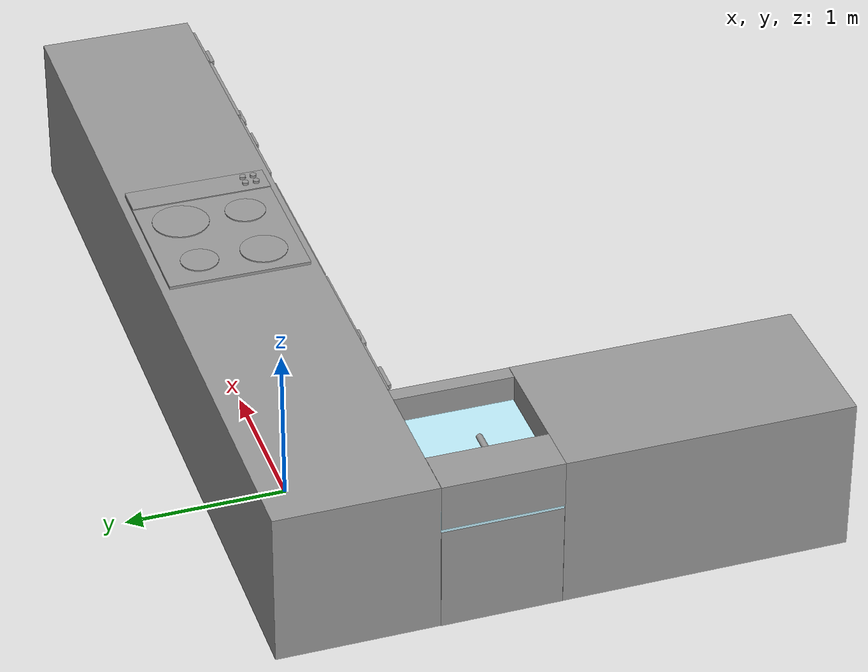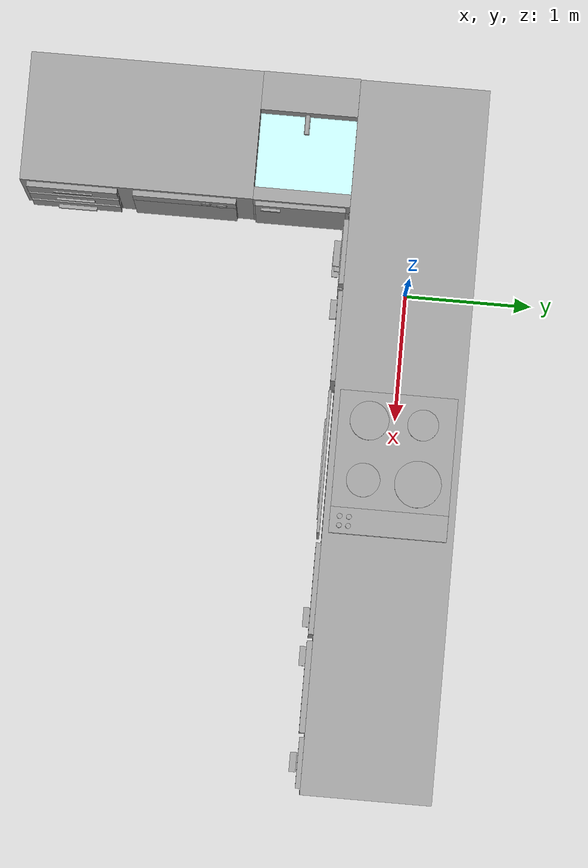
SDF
<?xml version='1.0'?>
<sdf version='1.7'>
  <model name='my_kitchen'>
    <link name='link'>
      <inertial>
        <mass>1</mass>
        <inertia>
          <ixx>0.166667</ixx>
          <ixy>0</ixy>
          <ixz>0</ixz>
          <iyy>0.166667</iyy>
          <iyz>0</iyz>
          <izz>0.166667</izz>
        </inertia>
        <pose>0 0 0 0 -0 0</pose>
      </inertial>
      <self_collide>0</self_collide>
      <enable_wind>0</enable_wind>
      <kinematic>0</kinematic>
      <pose>1.23923 -0.000128 0 0 -0 0</pose>
      <gravity>1</gravity>
      <visual name='visual'>
        <geometry>
          <box>
            <size>5.5 1 1</size>
          </box>
        </geometry>
        <material>
          <script>
            <name>Gazebo/Grey</name>
            <uri>file://media/materials/scripts/gazebo.material</uri>
          </script>
          <shader type='pixel'>
            <normal_map>__default__</normal_map>
          </shader>
          <ambient>0.8 0.8 0.8 1</ambient>
          <diffuse>0.65 0.65 0.65 1</diffuse>
          <specular>0.01 0.01 0.01 1</specular>
          <emissive>0 0 0 1</emissive>
        </material>
        <pose>0 0 0.5 0 -0 0</pose>
        <transparency>0</transparency>
        <cast_shadows>1</cast_shadows>
      </visual>
      <collision name='collision'>
        <laser_retro>0</laser_retro>
        <max_contacts>10</max_contacts>
        <pose>0 0 0.5 0 -0 0</pose>
        <geometry>
          <box>
            <size>5.5 1 1</size>
          </box>
        </geometry>
        <surface>
          <friction>
            <ode>
              <mu>1</mu>
              <mu2>1</mu2>
              <fdir1>0 0 0</fdir1>
              <slip1>0</slip1>
              <slip2>0</slip2>
            </ode>
            <torsional>
              <coefficient>1</coefficient>
              <patch_radius>0</patch_radius>
              <surface_radius>0</surface_radius>
              <use_patch_radius>1</use_patch_radius>
              <ode>
                <slip>0</slip>
              </ode>
            </torsional>
          </friction>
          <bounce>
            <restitution_coefficient>0</restitution_coefficient>
            <threshold>1e+06</threshold>
          </bounce>
          <contact>
            <collide_without_contact>0</collide_without_contact>
            <collide_without_contact_bitmask>1</collide_without_contact_bitmask>
            <collide_bitmask>1</collide_bitmask>
            <ode>
              <soft_cfm>0</soft_cfm>
              <soft_erp>0.2</soft_erp>
              <kp>1e+13</kp>
              <kd>1</kd>
              <max_vel>0.01</max_vel>
              <min_depth>0</min_depth>
            </ode>
            <bullet>
              <split_impulse>1</split_impulse>
              <split_impulse_penetration_threshold>-0.01</split_impulse_penetration_threshold>
              <soft_cfm>0</soft_cfm>
              <soft_erp>0.2</soft_erp>
              <kp>1e+13</kp>
              <kd>1</kd>
            </bullet>
          </contact>
        </surface>
      </collision>
    </link>
    <link name='link_0'>
      <inertial>
        <mass>1</mass>
        <inertia>
          <ixx>0.145833</ixx>
          <ixy>0</ixy>
          <ixz>0</ixz>
          <iyy>0.145833</iyy>
          <iyz>0</iyz>
          <izz>0.125</izz>
        </inertia>
        <pose>0 0 0 0 -0 0</pose>
      </inertial>
      <pose>-0.465747 -1.6095 0.842537 0 -0 0</pose>
      <gravity>1</gravity>
      <self_collide>0</self_collide>
      <kinematic>0</kinematic>
      <enable_wind>0</enable_wind>
      <visual name='visual'>
        <pose>0 0 0 0 1.5707 0</pose>
        <geometry>
          <cylinder>
            <radius>0.04</radius>
            <length>0.01</length>
          </cylinder>
        </geometry>
        <material>
          <lighting>1</lighting>
          <script>
            <uri>file://media/materials/scripts/gazebo.material</uri>
            <name>Gazebo/Grey</name>
          </script>
          <shader type='pixel'>
            <normal_map>__default__</normal_map>
          </shader>
          <ambient>0.9 0.9 0.9 1</ambient>
          <diffuse>0.9 0.9 0.9 1</diffuse>
          <specular>0.01 0.01 0.01 1</specular>
          <emissive>0 0 0 1</emissive>
        </material>
        <transparency>0</transparency>
        <cast_shadows>1</cast_shadows>
      </visual>
      <collision name='collision'>
        <laser_retro>0</laser_retro>
        <max_contacts>10</max_contacts>
        <pose>0 0 0 0 1.5707 0</pose>
        <geometry>
          <cylinder>
            <radius>0.04</radius>
            <length>0.01</length>
          </cylinder>
        </geometry>
        <surface>
          <friction>
            <ode>
              <mu>1</mu>
              <mu2>1</mu2>
              <fdir1>0 0 0</fdir1>
              <slip1>0</slip1>
              <slip2>0</slip2>
            </ode>
            <torsional>
              <coefficient>1</coefficient>
              <patch_radius>0</patch_radius>
              <surface_radius>0</surface_radius>
              <use_patch_radius>1</use_patch_radius>
              <ode>
                <slip>0</slip>
              </ode>
            </torsional>
          </friction>
          <bounce>
            <restitution_coefficient>0</restitution_coefficient>
            <threshold>1e+06</threshold>
          </bounce>
          <contact>
            <collide_without_contact>0</collide_without_contact>
            <collide_without_contact_bitmask>1</collide_without_contact_bitmask>
            <collide_bitmask>1</collide_bitmask>
            <ode>
              <soft_cfm>0</soft_cfm>
              <soft_erp>0.2</soft_erp>
              <kp>1e+13</kp>
              <kd>1</kd>
              <max_vel>0.01</max_vel>
              <min_depth>0</min_depth>
            </ode>
            <bullet>
              <split_impulse>1</split_impulse>
              <split_impulse_penetration_threshold>-0.01</split_impulse_penetration_threshold>
              <soft_cfm>0</soft_cfm>
              <soft_erp>0.2</soft_erp>
              <kp>1e+13</kp>
              <kd>1</kd>
            </bullet>
          </contact>
        </surface>
      </collision>
    </link>
    <link name='link_0_0'>
      <inertial>
        <mass>1</mass>
        <inertia>
          <ixx>0.145833</ixx>
          <ixy>0</ixy>
          <ixz>0</ixz>
          <iyy>0.145833</iyy>
          <iyz>0</iyz>
          <izz>0.125</izz>
        </inertia>
        <pose>0 0 0 0 -0 0</pose>
      </inertial>
      <pose>1.11587 -0.213264 1.02593 0 -0 0</pose>
      <gravity>0</gravity>
      <self_collide>0</self_collide>
      <kinematic>0</kinematic>
      <enable_wind>0</enable_wind>
      <visual name='visual'>
        <pose>0 0 0 0 -0 0</pose>
        <geometry>
          <cylinder>
            <radius>0.15</radius>
            <length>0.01</length>
          </cylinder>
        </geometry>
        <material>
          <lighting>1</lighting>
          <script>
            <uri>file://media/materials/scripts/gazebo.material</uri>
            <name>Gazebo/Grey</name>
          </script>
          <shader type='pixel'>
            <normal_map>__default__</normal_map>
          </shader>
          <ambient>0.3 0.3 0.3 1</ambient>
          <diffuse>0.3 0.3 0.3 1</diffuse>
          <specular>0.01 0.01 0.01 1</specular>
          <emissive>0 0 0 1</emissive>
        </material>
        <transparency>0</transparency>
        <cast_shadows>1</cast_shadows>
      </visual>
      <collision name='collision'>
        <laser_retro>0</laser_retro>
        <max_contacts>10</max_contacts>
        <pose>0 0 0 0 -0 0</pose>
        <geometry>
          <cylinder>
            <radius>0.15</radius>
            <length>0.01</length>
          </cylinder>
        </geometry>
        <surface>
          <friction>
            <ode>
              <mu>1</mu>
              <mu2>1</mu2>
              <fdir1>0 0 0</fdir1>
              <slip1>0</slip1>
              <slip2>0</slip2>
            </ode>
            <torsional>
              <coefficient>1</coefficient>
              <patch_radius>0</patch_radius>
              <surface_radius>0</surface_radius>
              <use_patch_radius>1</use_patch_radius>
              <ode>
                <slip>0</slip>
              </ode>
            </torsional>
          </friction>
          <bounce>
            <restitution_coefficient>0</restitution_coefficient>
            <threshold>1e+06</threshold>
          </bounce>
          <contact>
            <collide_without_contact>0</collide_without_contact>
            <collide_without_contact_bitmask>1</collide_without_contact_bitmask>
            <collide_bitmask>1</collide_bitmask>
            <ode>
              <soft_cfm>0</soft_cfm>
              <soft_erp>0.2</soft_erp>
              <kp>1e+13</kp>
              <kd>1</kd>
              <max_vel>0.01</max_vel>
              <min_depth>0</min_depth>
            </ode>
            <bullet>
              <split_impulse>1</split_impulse>
              <split_impulse_penetration_threshold>-0.01</split_impulse_penetration_threshold>
              <soft_cfm>0</soft_cfm>
              <soft_erp>0.2</soft_erp>
              <kp>1e+13</kp>
              <kd>1</kd>
            </bullet>
          </contact>
        </surface>
      </collision>
    </link>
    <link name='link_0_0_clone'>
      <inertial>
        <mass>1</mass>
        <inertia>
          <ixx>0.145833</ixx>
          <ixy>0</ixy>
          <ixz>0</ixz>
          <iyy>0.145833</iyy>
          <iyz>0</iyz>
          <izz>0.125</izz>
        </inertia>
        <pose>0 0 0 0 -0 0</pose>
      </inertial>
      <pose>1.11788 0.197131 1.02593 0 -0 0</pose>
      <gravity>0</gravity>
      <self_collide>0</self_collide>
      <kinematic>0</kinematic>
      <enable_wind>0</enable_wind>
      <visual name='visual'>
        <pose>0 0 0 0 -0 0</pose>
        <geometry>
          <cylinder>
            <radius>0.12</radius>
            <length>0.01</length>
          </cylinder>
        </geometry>
        <material>
          <lighting>1</lighting>
          <script>
            <uri>file://media/materials/scripts/gazebo.material</uri>
            <name>Gazebo/Grey</name>
          </script>
          <shader type='pixel'>
            <normal_map>__default__</normal_map>
          </shader>
          <ambient>0.3 0.3 0.3 1</ambient>
          <diffuse>0.3 0.3 0.3 1</diffuse>
          <specular>0.01 0.01 0.01 1</specular>
          <emissive>0 0 0 1</emissive>
        </material>
        <transparency>0</transparency>
        <cast_shadows>1</cast_shadows>
      </visual>
      <collision name='collision'>
        <laser_retro>0</laser_retro>
        <max_contacts>10</max_contacts>
        <pose>0 0 0 0 -0 0</pose>
        <geometry>
          <cylinder>
            <radius>0.12</radius>
            <length>0.01</length>
          </cylinder>
        </geometry>
        <surface>
          <friction>
            <ode>
              <mu>1</mu>
              <mu2>1</mu2>
              <fdir1>0 0 0</fdir1>
              <slip1>0</slip1>
              <slip2>0</slip2>
            </ode>
            <torsional>
              <coefficient>1</coefficient>
              <patch_radius>0</patch_radius>
              <surface_radius>0</surface_radius>
              <use_patch_radius>1</use_patch_radius>
              <ode>
                <slip>0</slip>
              </ode>
            </torsional>
          </friction>
          <bounce>
            <restitution_coefficient>0</restitution_coefficient>
            <threshold>1e+06</threshold>
          </bounce>
          <contact>
            <collide_without_contact>0</collide_without_contact>
            <collide_without_contact_bitmask>1</collide_without_contact_bitmask>
            <collide_bitmask>1</collide_bitmask>
            <ode>
              <soft_cfm>0</soft_cfm>
              <soft_erp>0.2</soft_erp>
              <kp>1e+13</kp>
              <kd>1</kd>
              <max_vel>0.01</max_vel>
              <min_depth>0</min_depth>
            </ode>
            <bullet>
              <split_impulse>1</split_impulse>
              <split_impulse_penetration_threshold>-0.01</split_impulse_penetration_threshold>
              <soft_cfm>0</soft_cfm>
              <soft_erp>0.2</soft_erp>
              <kp>1e+13</kp>
              <kd>1</kd>
            </bullet>
          </contact>
        </surface>
      </collision>
    </link>
    <link name='link_0_0_clone_clone'>
      <inertial>
        <mass>1</mass>
        <inertia>
          <ixx>0.145833</ixx>
          <ixy>0</ixy>
          <ixz>0</ixz>
          <iyy>0.145833</iyy>
          <iyz>0</iyz>
          <izz>0.125</izz>
        </inertia>
        <pose>0 0 0 0 -0 0</pose>
      </inertial>
      <pose>1.57169 0.194413 1.02593 0 -0 0</pose>
      <gravity>0</gravity>
      <self_collide>0</self_collide>
      <kinematic>0</kinematic>
      <enable_wind>0</enable_wind>
      <visual name='visual'>
        <pose>0 0 0 0 -0 0</pose>
        <geometry>
          <cylinder>
            <radius>0.18</radius>
            <length>0.01</length>
          </cylinder>
        </geometry>
        <material>
          <lighting>1</lighting>
          <script>
            <uri>file://media/materials/scripts/gazebo.material</uri>
            <name>Gazebo/Grey</name>
          </script>
          <shader type='pixel'>
            <normal_map>__default__</normal_map>
          </shader>
          <ambient>0.3 0.3 0.3 1</ambient>
          <diffuse>0.3 0.3 0.3 1</diffuse>
          <specular>0.01 0.01 0.01 1</specular>
          <emissive>0 0 0 1</emissive>
        </material>
        <transparency>0</transparency>
        <cast_shadows>1</cast_shadows>
      </visual>
      <collision name='collision'>
        <laser_retro>0</laser_retro>
        <max_contacts>10</max_contacts>
        <pose>0 0 0 0 -0 0</pose>
        <geometry>
          <cylinder>
            <radius>0.18</radius>
            <length>0.01</length>
          </cylinder>
        </geometry>
        <surface>
          <friction>
            <ode>
              <mu>1</mu>
              <mu2>1</mu2>
              <fdir1>0 0 0</fdir1>
              <slip1>0</slip1>
              <slip2>0</slip2>
            </ode>
            <torsional>
              <coefficient>1</coefficient>
              <patch_radius>0</patch_radius>
              <surface_radius>0</surface_radius>
              <use_patch_radius>1</use_patch_radius>
              <ode>
                <slip>0</slip>
              </ode>
            </torsional>
          </friction>
          <bounce>
            <restitution_coefficient>0</restitution_coefficient>
            <threshold>1e+06</threshold>
          </bounce>
          <contact>
            <collide_without_contact>0</collide_without_contact>
            <collide_without_contact_bitmask>1</collide_without_contact_bitmask>
            <collide_bitmask>1</collide_bitmask>
            <ode>
              <soft_cfm>0</soft_cfm>
              <soft_erp>0.2</soft_erp>
              <kp>1e+13</kp>
              <kd>1</kd>
              <max_vel>0.01</max_vel>
              <min_depth>0</min_depth>
            </ode>
            <bullet>
              <split_impulse>1</split_impulse>
              <split_impulse_penetration_threshold>-0.01</split_impulse_penetration_threshold>
              <soft_cfm>0</soft_cfm>
              <soft_erp>0.2</soft_erp>
              <kp>1e+13</kp>
              <kd>1</kd>
            </bullet>
          </contact>
        </surface>
      </collision>
    </link>
    <link name='link_0_0_clone_clone_clone'>
      <inertial>
        <mass>1</mass>
        <inertia>
          <ixx>0.145833</ixx>
          <ixy>0</ixy>
          <ixz>0</ixz>
          <iyy>0.145833</iyy>
          <iyz>0</iyz>
          <izz>0.125</izz>
        </inertia>
        <pose>0 0 0 0 -0 0</pose>
      </inertial>
      <pose>1.57274 -0.22407 1.02593 0 -0 0</pose>
      <gravity>0</gravity>
      <self_collide>0</self_collide>
      <kinematic>0</kinematic>
      <enable_wind>0</enable_wind>
      <visual name='visual'>
        <pose>0 0 0 0 -0 0</pose>
        <geometry>
          <cylinder>
            <radius>0.13</radius>
            <length>0.01</length>
          </cylinder>
        </geometry>
        <material>
          <lighting>1</lighting>
          <script>
            <uri>file://media/materials/scripts/gazebo.material</uri>
            <name>Gazebo/Grey</name>
          </script>
          <shader type='pixel'>
            <normal_map>__default__</normal_map>
          </shader>
          <ambient>0.3 0.3 0.3 1</ambient>
          <diffuse>0.3 0.3 0.3 1</diffuse>
          <specular>0.01 0.01 0.01 1</specular>
          <emissive>0 0 0 1</emissive>
        </material>
        <transparency>0</transparency>
        <cast_shadows>1</cast_shadows>
      </visual>
      <collision name='collision'>
        <laser_retro>0</laser_retro>
        <max_contacts>10</max_contacts>
        <pose>0 0 0 0 -0 0</pose>
        <geometry>
          <cylinder>
            <radius>0.13</radius>
            <length>0.01</length>
          </cylinder>
        </geometry>
        <surface>
          <friction>
            <ode>
              <mu>1</mu>
              <mu2>1</mu2>
              <fdir1>0 0 0</fdir1>
              <slip1>0</slip1>
              <slip2>0</slip2>
            </ode>
            <torsional>
              <coefficient>1</coefficient>
              <patch_radius>0</patch_radius>
              <surface_radius>0</surface_radius>
              <use_patch_radius>1</use_patch_radius>
              <ode>
                <slip>0</slip>
              </ode>
            </torsional>
          </friction>
          <bounce>
            <restitution_coefficient>0</restitution_coefficient>
            <threshold>1e+06</threshold>
          </bounce>
          <contact>
            <collide_without_contact>0</collide_without_contact>
            <collide_without_contact_bitmask>1</collide_without_contact_bitmask>
            <collide_bitmask>1</collide_bitmask>
            <ode>
              <soft_cfm>0</soft_cfm>
              <soft_erp>0.2</soft_erp>
              <kp>1e+13</kp>
              <kd>1</kd>
              <max_vel>0.01</max_vel>
              <min_depth>0</min_depth>
            </ode>
            <bullet>
              <split_impulse>1</split_impulse>
              <split_impulse_penetration_threshold>-0.01</split_impulse_penetration_threshold>
              <soft_cfm>0</soft_cfm>
              <soft_erp>0.2</soft_erp>
              <kp>1e+13</kp>
              <kd>1</kd>
            </bullet>
          </contact>
        </surface>
      </collision>
    </link>
    <link name='link_0_0_clone_clone_clone_clone'>
      <inertial>
        <mass>1</mass>
        <inertia>
          <ixx>0.145833</ixx>
          <ixy>0</ixy>
          <ixz>0</ixz>
          <iyy>0.145833</iyy>
          <iyz>0</iyz>
          <izz>0.125</izz>
        </inertia>
        <pose>0 0 0 0 -0 0</pose>
      </inertial>
      <pose>1.86316 -0.307981 1.03286 0 -0 0</pose>
      <gravity>1</gravity>
      <self_collide>0</self_collide>
      <kinematic>0</kinematic>
      <enable_wind>0</enable_wind>
      <visual name='visual'>
        <pose>0 0 0 0 -0 0</pose>
        <geometry>
          <cylinder>
            <radius>0.02</radius>
            <length>0.03</length>
          </cylinder>
        </geometry>
        <material>
          <lighting>1</lighting>
          <script>
            <uri>file://media/materials/scripts/gazebo.material</uri>
            <name>Gazebo/Grey</name>
          </script>
          <shader type='pixel'>
            <normal_map>__default__</normal_map>
          </shader>
          <ambient>0.6 0.6 0.6 1</ambient>
          <diffuse>0.6 0.6 0.6 1</diffuse>
          <specular>0.01 0.01 0.01 1</specular>
          <emissive>0 0 0 1</emissive>
        </material>
        <transparency>0</transparency>
        <cast_shadows>1</cast_shadows>
      </visual>
      <collision name='collision'>
        <laser_retro>0</laser_retro>
        <max_contacts>10</max_contacts>
        <pose>0 0 0 0 -0 0</pose>
        <geometry>
          <cylinder>
            <radius>0.02</radius>
            <length>0.03</length>
          </cylinder>
        </geometry>
        <surface>
          <friction>
            <ode>
              <mu>1</mu>
              <mu2>1</mu2>
              <fdir1>0 0 0</fdir1>
              <slip1>0</slip1>
              <slip2>0</slip2>
            </ode>
            <torsional>
              <coefficient>1</coefficient>
              <patch_radius>0</patch_radius>
              <surface_radius>0</surface_radius>
              <use_patch_radius>1</use_patch_radius>
              <ode>
                <slip>0</slip>
              </ode>
            </torsional>
          </friction>
          <bounce>
            <restitution_coefficient>0</restitution_coefficient>
            <threshold>1e+06</threshold>
          </bounce>
          <contact>
            <collide_without_contact>0</collide_without_contact>
            <collide_without_contact_bitmask>1</collide_without_contact_bitmask>
            <collide_bitmask>1</collide_bitmask>
            <ode>
              <soft_cfm>0</soft_cfm>
              <soft_erp>0.2</soft_erp>
              <kp>1e+13</kp>
              <kd>1</kd>
              <max_vel>0.01</max_vel>
              <min_depth>0</min_depth>
            </ode>
            <bullet>
              <split_impulse>1</split_impulse>
              <split_impulse_penetration_threshold>-0.01</split_impulse_penetration_threshold>
              <soft_cfm>0</soft_cfm>
              <soft_erp>0.2</soft_erp>
              <kp>1e+13</kp>
              <kd>1</kd>
            </bullet>
          </contact>
        </surface>
      </collision>
    </link>
    <link name='link_0_0_clone_clone_clone_clone_clone'>
      <inertial>
        <mass>1</mass>
        <inertia>
          <ixx>0.145833</ixx>
          <ixy>0</ixy>
          <ixz>0</ixz>
          <iyy>0.145833</iyy>
          <iyz>0</iyz>
          <izz>0.125</izz>
        </inertia>
        <pose>0 0 0 0 -0 0</pose>
      </inertial>
      <pose>1.93281 -0.308649 1.03286 0 -0 0</pose>
      <gravity>1</gravity>
      <self_collide>0</self_collide>
      <kinematic>0</kinematic>
      <enable_wind>0</enable_wind>
      <visual name='visual'>
        <pose>0 0 0 0 -0 0</pose>
        <geometry>
          <cylinder>
            <radius>0.02</radius>
            <length>0.03</length>
          </cylinder>
        </geometry>
        <material>
          <lighting>1</lighting>
          <script>
            <uri>file://media/materials/scripts/gazebo.material</uri>
            <name>Gazebo/Grey</name>
          </script>
          <shader type='pixel'>
            <normal_map>__default__</normal_map>
          </shader>
          <ambient>0.6 0.6 0.6 1</ambient>
          <diffuse>0.6 0.6 0.6 1</diffuse>
          <specular>0.01 0.01 0.01 1</specular>
          <emissive>0 0 0 1</emissive>
        </material>
        <transparency>0</transparency>
        <cast_shadows>1</cast_shadows>
      </visual>
      <collision name='collision'>
        <laser_retro>0</laser_retro>
        <max_contacts>10</max_contacts>
        <pose>0 0 0 0 -0 0</pose>
        <geometry>
          <cylinder>
            <radius>0.02</radius>
            <length>0.03</length>
          </cylinder>
        </geometry>
        <surface>
          <friction>
            <ode>
              <mu>1</mu>
              <mu2>1</mu2>
              <fdir1>0 0 0</fdir1>
              <slip1>0</slip1>
              <slip2>0</slip2>
            </ode>
            <torsional>
              <coefficient>1</coefficient>
              <patch_radius>0</patch_radius>
              <surface_radius>0</surface_radius>
              <use_patch_radius>1</use_patch_radius>
              <ode>
                <slip>0</slip>
              </ode>
            </torsional>
          </friction>
          <bounce>
            <restitution_coefficient>0</restitution_coefficient>
            <threshold>1e+06</threshold>
          </bounce>
          <contact>
            <collide_without_contact>0</collide_without_contact>
            <collide_without_contact_bitmask>1</collide_without_contact_bitmask>
            <collide_bitmask>1</collide_bitmask>
            <ode>
              <soft_cfm>0</soft_cfm>
              <soft_erp>0.2</soft_erp>
              <kp>1e+13</kp>
              <kd>1</kd>
              <max_vel>0.01</max_vel>
              <min_depth>0</min_depth>
            </ode>
            <bullet>
              <split_impulse>1</split_impulse>
              <split_impulse_penetration_threshold>-0.01</split_impulse_penetration_threshold>
              <soft_cfm>0</soft_cfm>
              <soft_erp>0.2</soft_erp>
              <kp>1e+13</kp>
              <kd>1</kd>
            </bullet>
          </contact>
        </surface>
      </collision>
    </link>
    <link name='link_0_0_clone_clone_clone_clone_clone_clone'>
      <inertial>
        <mass>1</mass>
        <inertia>
          <ixx>0.145833</ixx>
          <ixy>0</ixy>
          <ixz>0</ixz>
          <iyy>0.145833</iyy>
          <iyz>0</iyz>
          <izz>0.125</izz>
        </inertia>
        <pose>0 0 0 0 -0 0</pose>
      </inertial>
      <pose>1.86215 -0.379023 1.03286 0 -0 0</pose>
      <gravity>1</gravity>
      <self_collide>0</self_collide>
      <kinematic>0</kinematic>
      <enable_wind>0</enable_wind>
      <visual name='visual'>
        <pose>0 0 0 0 -0 0</pose>
        <geometry>
          <cylinder>
            <radius>0.02</radius>
            <length>0.03</length>
          </cylinder>
        </geometry>
        <material>
          <lighting>1</lighting>
          <script>
            <uri>file://media/materials/scripts/gazebo.material</uri>
            <name>Gazebo/Grey</name>
          </script>
          <shader type='pixel'>
            <normal_map>__default__</normal_map>
          </shader>
          <ambient>0.6 0.6 0.6 1</ambient>
          <diffuse>0.6 0.6 0.6 1</diffuse>
          <specular>0.01 0.01 0.01 1</specular>
          <emissive>0 0 0 1</emissive>
        </material>
        <transparency>0</transparency>
        <cast_shadows>1</cast_shadows>
      </visual>
      <collision name='collision'>
        <laser_retro>0</laser_retro>
        <max_contacts>10</max_contacts>
        <pose>0 0 0 0 -0 0</pose>
        <geometry>
          <cylinder>
            <radius>0.02</radius>
            <length>0.03</length>
          </cylinder>
        </geometry>
        <surface>
          <friction>
            <ode>
              <mu>1</mu>
              <mu2>1</mu2>
              <fdir1>0 0 0</fdir1>
              <slip1>0</slip1>
              <slip2>0</slip2>
            </ode>
            <torsional>
              <coefficient>1</coefficient>
              <patch_radius>0</patch_radius>
              <surface_radius>0</surface_radius>
              <use_patch_radius>1</use_patch_radius>
              <ode>
                <slip>0</slip>
              </ode>
            </torsional>
          </friction>
          <bounce>
            <restitution_coefficient>0</restitution_coefficient>
            <threshold>1e+06</threshold>
          </bounce>
          <contact>
            <collide_without_contact>0</collide_without_contact>
            <collide_without_contact_bitmask>1</collide_without_contact_bitmask>
            <collide_bitmask>1</collide_bitmask>
            <ode>
              <soft_cfm>0</soft_cfm>
              <soft_erp>0.2</soft_erp>
              <kp>1e+13</kp>
              <kd>1</kd>
              <max_vel>0.01</max_vel>
              <min_depth>0</min_depth>
            </ode>
            <bullet>
              <split_impulse>1</split_impulse>
              <split_impulse_penetration_threshold>-0.01</split_impulse_penetration_threshold>
              <soft_cfm>0</soft_cfm>
              <soft_erp>0.2</soft_erp>
              <kp>1e+13</kp>
              <kd>1</kd>
            </bullet>
          </contact>
        </surface>
      </collision>
    </link>
    <link name='link_0_0_clone_clone_clone_clone_clone_clone_clone'>
      <inertial>
        <mass>1</mass>
        <inertia>
          <ixx>0.145833</ixx>
          <ixy>0</ixy>
          <ixz>0</ixz>
          <iyy>0.145833</iyy>
          <iyz>0</iyz>
          <izz>0.125</izz>
        </inertia>
        <pose>0 0 0 0 -0 0</pose>
      </inertial>
      <pose>1.93241 -0.377735 1.03286 0 -0 0</pose>
      <gravity>1</gravity>
      <self_collide>0</self_collide>
      <kinematic>0</kinematic>
      <enable_wind>0</enable_wind>
      <visual name='visual'>
        <pose>0 0 0 0 -0 0</pose>
        <geometry>
          <cylinder>
            <radius>0.02</radius>
            <length>0.03</length>
          </cylinder>
        </geometry>
        <material>
          <lighting>1</lighting>
          <script>
            <uri>file://media/materials/scripts/gazebo.material</uri>
            <name>Gazebo/Grey</name>
          </script>
          <shader type='pixel'>
            <normal_map>__default__</normal_map>
          </shader>
          <ambient>0.6 0.6 0.6 1</ambient>
          <diffuse>0.6 0.6 0.6 1</diffuse>
          <specular>0.01 0.01 0.01 1</specular>
          <emissive>0 0 0 1</emissive>
        </material>
        <transparency>0</transparency>
        <cast_shadows>1</cast_shadows>
      </visual>
      <collision name='collision'>
        <laser_retro>0</laser_retro>
        <max_contacts>10</max_contacts>
        <pose>0 0 0 0 -0 0</pose>
        <geometry>
          <cylinder>
            <radius>0.02</radius>
            <length>0.03</length>
          </cylinder>
        </geometry>
        <surface>
          <friction>
            <ode>
              <mu>1</mu>
              <mu2>1</mu2>
              <fdir1>0 0 0</fdir1>
              <slip1>0</slip1>
              <slip2>0</slip2>
            </ode>
            <torsional>
              <coefficient>1</coefficient>
              <patch_radius>0</patch_radius>
              <surface_radius>0</surface_radius>
              <use_patch_radius>1</use_patch_radius>
              <ode>
                <slip>0</slip>
              </ode>
            </torsional>
          </friction>
          <bounce>
            <restitution_coefficient>0</restitution_coefficient>
            <threshold>1e+06</threshold>
          </bounce>
          <contact>
            <collide_without_contact>0</collide_without_contact>
            <collide_without_contact_bitmask>1</collide_without_contact_bitmask>
            <collide_bitmask>1</collide_bitmask>
            <ode>
              <soft_cfm>0</soft_cfm>
              <soft_erp>0.2</soft_erp>
              <kp>1e+13</kp>
              <kd>1</kd>
              <max_vel>0.01</max_vel>
              <min_depth>0</min_depth>
            </ode>
            <bullet>
              <split_impulse>1</split_impulse>
              <split_impulse_penetration_threshold>-0.01</split_impulse_penetration_threshold>
              <soft_cfm>0</soft_cfm>
              <soft_erp>0.2</soft_erp>
              <kp>1e+13</kp>
              <kd>1</kd>
            </bullet>
          </contact>
        </surface>
      </collision>
    </link>
    <link name='link_0_clone'>
      <inertial>
        <mass>1</mass>
        <inertia>
          <ixx>0.145833</ixx>
          <ixy>0</ixy>
          <ixz>0</ixz>
          <iyy>0.145833</iyy>
          <iyz>0</iyz>
          <izz>0.125</izz>
        </inertia>
        <pose>0 0 0 0 -0 0</pose>
      </inertial>
      <pose>-1.12966 -0.882077 0.956076 0 -0 0</pose>
      <gravity>0</gravity>
      <self_collide>0</self_collide>
      <kinematic>0</kinematic>
      <enable_wind>0</enable_wind>
      <visual name='visual'>
        <pose>0 0 0 0 1.5707 0</pose>
        <geometry>
          <cylinder>
            <radius>0.02</radius>
            <length>0.15</length>
          </cylinder>
        </geometry>
        <material>
          <lighting>1</lighting>
          <script>
            <uri>file://media/materials/scripts/gazebo.material</uri>
            <name>Gazebo/Grey</name>
          </script>
          <shader type='pixel'>
            <normal_map>__default__</normal_map>
          </shader>
          <ambient>0.2 0.2 0.2 1</ambient>
          <diffuse>0.2 0.2 0.2 1</diffuse>
          <specular>0.01 0.01 0.01 1</specular>
          <emissive>0 0 0 1</emissive>
        </material>
        <transparency>0</transparency>
        <cast_shadows>1</cast_shadows>
      </visual>
      <collision name='collision'>
        <laser_retro>0</laser_retro>
        <max_contacts>10</max_contacts>
        <pose>0 0 0 0 1.5707 0</pose>
        <geometry>
          <cylinder>
            <radius>0.02</radius>
            <length>0.15</length>
          </cylinder>
        </geometry>
        <surface>
          <friction>
            <ode>
              <mu>1</mu>
              <mu2>1</mu2>
              <fdir1>0 0 0</fdir1>
              <slip1>0</slip1>
              <slip2>0</slip2>
            </ode>
            <torsional>
              <coefficient>1</coefficient>
              <patch_radius>0</patch_radius>
              <surface_radius>0</surface_radius>
              <use_patch_radius>1</use_patch_radius>
              <ode>
                <slip>0</slip>
              </ode>
            </torsional>
          </friction>
          <bounce>
            <restitution_coefficient>0</restitution_coefficient>
            <threshold>1e+06</threshold>
          </bounce>
          <contact>
            <collide_without_contact>0</collide_without_contact>
            <collide_without_contact_bitmask>1</collide_without_contact_bitmask>
            <collide_bitmask>1</collide_bitmask>
            <ode>
              <soft_cfm>0</soft_cfm>
              <soft_erp>0.2</soft_erp>
              <kp>1e+13</kp>
              <kd>1</kd>
              <max_vel>0.01</max_vel>
              <min_depth>0</min_depth>
            </ode>
            <bullet>
              <split_impulse>1</split_impulse>
              <split_impulse_penetration_threshold>-0.01</split_impulse_penetration_threshold>
              <soft_cfm>0</soft_cfm>
              <soft_erp>0.2</soft_erp>
              <kp>1e+13</kp>
              <kd>1</kd>
            </bullet>
          </contact>
        </surface>
      </collision>
    </link>
    <link name='link_0_clone_0'>
      <inertial>
        <mass>1</mass>
        <inertia>
          <ixx>0.145833</ixx>
          <ixy>0</ixy>
          <ixz>0</ixz>
          <iyy>0.145833</iyy>
          <iyz>0</iyz>
          <izz>0.125</izz>
        </inertia>
        <pose>0 0 0 0 -0 0</pose>
      </inertial>
      <pose>-0.459347 -1.48795 0.840731 0 -0 0</pose>
      <gravity>1</gravity>
      <self_collide>0</self_collide>
      <kinematic>0</kinematic>
      <enable_wind>0</enable_wind>
      <visual name='visual'>
        <pose>0 0 0 0 1.5707 0</pose>
        <geometry>
          <cylinder>
            <radius>0.04</radius>
            <length>0.01</length>
          </cylinder>
        </geometry>
        <material>
          <lighting>1</lighting>
          <script>
            <uri>file://media/materials/scripts/gazebo.material</uri>
            <name>Gazebo/Grey</name>
          </script>
          <shader type='pixel'>
            <normal_map>__default__</normal_map>
          </shader>
          <ambient>0.9 0.9 0.9 1</ambient>
          <diffuse>0.9 0.9 0.9 1</diffuse>
          <specular>0.01 0.01 0.01 1</specular>
          <emissive>0 0 0 1</emissive>
        </material>
        <transparency>0</transparency>
        <cast_shadows>1</cast_shadows>
      </visual>
      <collision name='collision'>
        <laser_retro>0</laser_retro>
        <max_contacts>10</max_contacts>
        <pose>0 0 0 0 1.5707 0</pose>
        <geometry>
          <cylinder>
            <radius>0.04</radius>
            <length>0.01</length>
          </cylinder>
        </geometry>
        <surface>
          <friction>
            <ode>
              <mu>1</mu>
              <mu2>1</mu2>
              <fdir1>0 0 0</fdir1>
              <slip1>0</slip1>
              <slip2>0</slip2>
            </ode>
            <torsional>
              <coefficient>1</coefficient>
              <patch_radius>0</patch_radius>
              <surface_radius>0</surface_radius>
              <use_patch_radius>1</use_patch_radius>
              <ode>
                <slip>0</slip>
              </ode>
            </torsional>
          </friction>
          <bounce>
            <restitution_coefficient>0</restitution_coefficient>
            <threshold>1e+06</threshold>
          </bounce>
          <contact>
            <collide_without_contact>0</collide_without_contact>
            <collide_without_contact_bitmask>1</collide_without_contact_bitmask>
            <collide_bitmask>1</collide_bitmask>
            <ode>
              <soft_cfm>0</soft_cfm>
              <soft_erp>0.2</soft_erp>
              <kp>1e+13</kp>
              <kd>1</kd>
              <max_vel>0.01</max_vel>
              <min_depth>0</min_depth>
            </ode>
            <bullet>
              <split_impulse>1</split_impulse>
              <split_impulse_penetration_threshold>-0.01</split_impulse_penetration_threshold>
              <soft_cfm>0</soft_cfm>
              <soft_erp>0.2</soft_erp>
              <kp>1e+13</kp>
              <kd>1</kd>
            </bullet>
          </contact>
        </surface>
      </collision>
    </link>
    <link name='link_0_clone_1'>
      <inertial>
        <mass>1</mass>
        <inertia>
          <ixx>0.145833</ixx>
          <ixy>0</ixy>
          <ixz>0</ixz>
          <iyy>0.145833</iyy>
          <iyz>0</iyz>
          <izz>0.125</izz>
        </inertia>
        <pose>0 0 0 0 -0 0</pose>
      </inertial>
      <pose>1.8493 -0.544143 0.806367 0 -0 0</pose>
      <gravity>1</gravity>
      <self_collide>0</self_collide>
      <kinematic>0</kinematic>
      <enable_wind>0</enable_wind>
      <visual name='visual'>
        <pose>0 0 0 1.57013 1.5707 -0.000572</pose>
        <geometry>
          <cylinder>
            <radius>0.04</radius>
            <length>0.01</length>
          </cylinder>
        </geometry>
        <material>
          <lighting>1</lighting>
          <script>
            <uri>file://media/materials/scripts/gazebo.material</uri>
            <name>Gazebo/Grey</name>
          </script>
          <shader type='pixel'>
            <normal_map>__default__</normal_map>
          </shader>
          <ambient>0.9 0.9 0.9 1</ambient>
          <diffuse>0.9 0.9 0.9 1</diffuse>
          <specular>0.01 0.01 0.01 1</specular>
          <emissive>0 0 0 1</emissive>
        </material>
        <transparency>0</transparency>
        <cast_shadows>1</cast_shadows>
      </visual>
      <collision name='collision'>
        <laser_retro>0</laser_retro>
        <max_contacts>10</max_contacts>
        <pose>0 0 0 1.5707 1.5707 -0</pose>
        <geometry>
          <cylinder>
            <radius>0.04</radius>
            <length>0.01</length>
          </cylinder>
        </geometry>
        <surface>
          <friction>
            <ode>
              <mu>1</mu>
              <mu2>1</mu2>
              <fdir1>0 0 0</fdir1>
              <slip1>0</slip1>
              <slip2>0</slip2>
            </ode>
            <torsional>
              <coefficient>1</coefficient>
              <patch_radius>0</patch_radius>
              <surface_radius>0</surface_radius>
              <use_patch_radius>1</use_patch_radius>
              <ode>
                <slip>0</slip>
              </ode>
            </torsional>
          </friction>
          <bounce>
            <restitution_coefficient>0</restitution_coefficient>
            <threshold>1e+06</threshold>
          </bounce>
          <contact>
            <collide_without_contact>0</collide_without_contact>
            <collide_without_contact_bitmask>1</collide_without_contact_bitmask>
            <collide_bitmask>1</collide_bitmask>
            <ode>
              <soft_cfm>0</soft_cfm>
              <soft_erp>0.2</soft_erp>
              <kp>1e+13</kp>
              <kd>1</kd>
              <max_vel>0.01</max_vel>
              <min_depth>0</min_depth>
            </ode>
            <bullet>
              <split_impulse>1</split_impulse>
              <split_impulse_penetration_threshold>-0.01</split_impulse_penetration_threshold>
              <soft_cfm>0</soft_cfm>
              <soft_erp>0.2</soft_erp>
              <kp>1e+13</kp>
              <kd>1</kd>
            </bullet>
          </contact>
        </surface>
      </collision>
    </link>
    <link name='link_0_clone_1_clone'>
      <inertial>
        <mass>1</mass>
        <inertia>
          <ixx>0.145833</ixx>
          <ixy>0</ixy>
          <ixz>0</ixz>
          <iyy>0.145833</iyy>
          <iyz>0</iyz>
          <izz>0.125</izz>
        </inertia>
        <pose>0 0 0 0 -0 0</pose>
      </inertial>
      <pose>1.72105 -0.544038 0.809821 0 -0 0</pose>
      <gravity>1</gravity>
      <self_collide>0</self_collide>
      <kinematic>0</kinematic>
      <enable_wind>0</enable_wind>
      <visual name='visual'>
        <pose>0 0 0 1.57013 1.5707 -0.000572</pose>
        <geometry>
          <cylinder>
            <radius>0.04</radius>
            <length>0.01</length>
          </cylinder>
        </geometry>
        <material>
          <lighting>1</lighting>
          <script>
            <uri>file://media/materials/scripts/gazebo.material</uri>
            <name>Gazebo/Grey</name>
          </script>
          <shader type='pixel'>
            <normal_map>__default__</normal_map>
          </shader>
          <ambient>0.9 0.9 0.9 1</ambient>
          <diffuse>0.9 0.9 0.9 1</diffuse>
          <specular>0.01 0.01 0.01 1</specular>
          <emissive>0 0 0 1</emissive>
        </material>
        <transparency>0</transparency>
        <cast_shadows>1</cast_shadows>
      </visual>
      <collision name='collision'>
        <laser_retro>0</laser_retro>
        <max_contacts>10</max_contacts>
        <pose>0 0 0 1.57013 1.5707 -0.000572</pose>
        <geometry>
          <cylinder>
            <radius>0.04</radius>
            <length>0.01</length>
          </cylinder>
        </geometry>
        <surface>
          <friction>
            <ode>
              <mu>1</mu>
              <mu2>1</mu2>
              <fdir1>0 0 0</fdir1>
              <slip1>0</slip1>
              <slip2>0</slip2>
            </ode>
            <torsional>
              <coefficient>1</coefficient>
              <patch_radius>0</patch_radius>
              <surface_radius>0</surface_radius>
              <use_patch_radius>1</use_patch_radius>
              <ode>
                <slip>0</slip>
              </ode>
            </torsional>
          </friction>
          <bounce>
            <restitution_coefficient>0</restitution_coefficient>
            <threshold>1e+06</threshold>
          </bounce>
          <contact>
            <collide_without_contact>0</collide_without_contact>
            <collide_without_contact_bitmask>1</collide_without_contact_bitmask>
            <collide_bitmask>1</collide_bitmask>
            <ode>
              <soft_cfm>0</soft_cfm>
              <soft_erp>0.2</soft_erp>
              <kp>1e+13</kp>
              <kd>1</kd>
              <max_vel>0.01</max_vel>
              <min_depth>0</min_depth>
            </ode>
            <bullet>
              <split_impulse>1</split_impulse>
              <split_impulse_penetration_threshold>-0.01</split_impulse_penetration_threshold>
              <soft_cfm>0</soft_cfm>
              <soft_erp>0.2</soft_erp>
              <kp>1e+13</kp>
              <kd>1</kd>
            </bullet>
          </contact>
        </surface>
      </collision>
    </link>
    <link name='link_clone'>
      <inertial>
        <mass>1</mass>
        <inertia>
          <ixx>0.166667</ixx>
          <ixy>0</ixy>
          <ixz>0</ixz>
          <iyy>0.166667</iyy>
          <iyz>0</iyz>
          <izz>0.166667</izz>
        </inertia>
        <pose>0 0 0 0 -0 0</pose>
      </inertial>
      <self_collide>0</self_collide>
      <enable_wind>0</enable_wind>
      <kinematic>0</kinematic>
      <pose>-1.0136 -2.15012 0 0 -0 0</pose>
      <gravity>1</gravity>
      <visual name='visual'>
        <geometry>
          <box>
            <size>1 1.8 1</size>
          </box>
        </geometry>
        <material>
          <script>
            <name>Gazebo/Grey</name>
            <uri>file://media/materials/scripts/gazebo.material</uri>
          </script>
          <shader type='pixel'>
            <normal_map>__default__</normal_map>
          </shader>
          <ambient>0.8 0.8 0.8 1</ambient>
          <diffuse>0.65 0.65 0.65 1</diffuse>
          <specular>0.01 0.01 0.01 1</specular>
          <emissive>0 0 0 1</emissive>
        </material>
        <pose>0 0 0.5 0 -0 0</pose>
        <transparency>0</transparency>
        <cast_shadows>1</cast_shadows>
      </visual>
      <collision name='collision'>
        <laser_retro>0</laser_retro>
        <max_contacts>10</max_contacts>
        <pose>0 0 0.5 0 -0 0</pose>
        <geometry>
          <box>
            <size>1 1.8 1</size>
          </box>
        </geometry>
        <surface>
          <friction>
            <ode>
              <mu>1</mu>
              <mu2>1</mu2>
              <fdir1>0 0 0</fdir1>
              <slip1>0</slip1>
              <slip2>0</slip2>
            </ode>
            <torsional>
              <coefficient>1</coefficient>
              <patch_radius>0</patch_radius>
              <surface_radius>0</surface_radius>
              <use_patch_radius>1</use_patch_radius>
              <ode>
                <slip>0</slip>
              </ode>
            </torsional>
          </friction>
          <bounce>
            <restitution_coefficient>0</restitution_coefficient>
            <threshold>1e+06</threshold>
          </bounce>
          <contact>
            <collide_without_contact>0</collide_without_contact>
            <collide_without_contact_bitmask>1</collide_without_contact_bitmask>
            <collide_bitmask>1</collide_bitmask>
            <ode>
              <soft_cfm>0</soft_cfm>
              <soft_erp>0.2</soft_erp>
              <kp>1e+13</kp>
              <kd>1</kd>
              <max_vel>0.01</max_vel>
              <min_depth>0</min_depth>
            </ode>
            <bullet>
              <split_impulse>1</split_impulse>
              <split_impulse_penetration_threshold>-0.01</split_impulse_penetration_threshold>
              <soft_cfm>0</soft_cfm>
              <soft_erp>0.2</soft_erp>
              <kp>1e+13</kp>
              <kd>1</kd>
            </bullet>
          </contact>
        </surface>
      </collision>
    </link>
    <link name='link_clone_0'>
      <inertial>
        <mass>1</mass>
        <inertia>
          <ixx>0.166667</ixx>
          <ixy>0</ixy>
          <ixz>0</ixz>
          <iyy>0.166667</iyy>
          <iyz>0</iyz>
          <izz>0.166667</izz>
        </inertia>
        <pose>0 0 0 0 -0 0</pose>
      </inertial>
      <self_collide>0</self_collide>
      <enable_wind>0</enable_wind>
      <kinematic>0</kinematic>
      <pose>1.44437 -0.002505 0.513121 0 -0 0</pose>
      <gravity>0</gravity>
      <visual name='visual'>
        <geometry>
          <box>
            <size>1.1 0.9 0.02</size>
          </box>
        </geometry>
        <material>
          <script>
            <name>Gazebo/Grey</name>
            <uri>file://media/materials/scripts/gazebo.material</uri>
          </script>
          <shader type='pixel'>
            <normal_map>__default__</normal_map>
          </shader>
          <ambient>0.2 0.2 0.2 1</ambient>
          <diffuse>0.2 0.2 0.2 1</diffuse>
          <specular>0.01 0.01 0.01 1</specular>
          <emissive>0 0 0 1</emissive>
        </material>
        <pose>0 0 0.5 0 -0 0</pose>
        <transparency>0</transparency>
        <cast_shadows>1</cast_shadows>
      </visual>
      <collision name='collision'>
        <laser_retro>0</laser_retro>
        <max_contacts>10</max_contacts>
        <pose>0 0 0.5 0 -0 0</pose>
        <geometry>
          <box>
            <size>1.1 0.9 0.02</size>
          </box>
        </geometry>
        <surface>
          <friction>
            <ode>
              <mu>1</mu>
              <mu2>1</mu2>
              <fdir1>0 0 0</fdir1>
              <slip1>0</slip1>
              <slip2>0</slip2>
            </ode>
            <torsional>
              <coefficient>1</coefficient>
              <patch_radius>0</patch_radius>
              <surface_radius>0</surface_radius>
              <use_patch_radius>1</use_patch_radius>
              <ode>
                <slip>0</slip>
              </ode>
            </torsional>
          </friction>
          <bounce>
            <restitution_coefficient>0</restitution_coefficient>
            <threshold>1e+06</threshold>
          </bounce>
          <contact>
            <collide_without_contact>0</collide_without_contact>
            <collide_without_contact_bitmask>1</collide_without_contact_bitmask>
            <collide_bitmask>1</collide_bitmask>
            <ode>
              <soft_cfm>0</soft_cfm>
              <soft_erp>0.2</soft_erp>
              <kp>1e+13</kp>
              <kd>1</kd>
              <max_vel>0.01</max_vel>
              <min_depth>0</min_depth>
            </ode>
            <bullet>
              <split_impulse>1</split_impulse>
              <split_impulse_penetration_threshold>-0.01</split_impulse_penetration_threshold>
              <soft_cfm>0</soft_cfm>
              <soft_erp>0.2</soft_erp>
              <kp>1e+13</kp>
              <kd>1</kd>
            </bullet>
          </contact>
        </surface>
      </collision>
    </link>
    <link name='link_clone_0_clone'>
      <inertial>
        <mass>1</mass>
        <inertia>
          <ixx>0.166667</ixx>
          <ixy>0</ixy>
          <ixz>0</ixz>
          <iyy>0.166667</iyy>
          <iyz>0</iyz>
          <izz>0.166667</izz>
        </inertia>
        <pose>0 0 0 0 -0 0</pose>
      </inertial>
      <self_collide>0</self_collide>
      <enable_wind>0</enable_wind>
      <kinematic>0</kinematic>
      <pose>1.89193 -0.003715 0.520133 0 -0 0</pose>
      <gravity>0</gravity>
      <visual name='visual'>
        <geometry>
          <box>
            <size>0.2 0.9 0.02</size>
          </box>
        </geometry>
        <material>
          <script>
            <name>Gazebo/Grey</name>
            <uri>file://media/materials/scripts/gazebo.material</uri>
          </script>
          <shader type='pixel'>
            <normal_map>__default__</normal_map>
          </shader>
          <ambient>0.4 0.4 0.4 1</ambient>
          <diffuse>0.4 0.4 0.4 1</diffuse>
          <specular>0.01 0.01 0.01 1</specular>
          <emissive>0 0 0 1</emissive>
        </material>
        <pose>0 0 0.5 0 -0 0</pose>
        <transparency>0</transparency>
        <cast_shadows>1</cast_shadows>
      </visual>
      <collision name='collision'>
        <laser_retro>0</laser_retro>
        <max_contacts>10</max_contacts>
        <pose>0 0 0.5 0 -0 0</pose>
        <geometry>
          <box>
            <size>0.2 0.9 0.02</size>
          </box>
        </geometry>
        <surface>
          <friction>
            <ode>
              <mu>1</mu>
              <mu2>1</mu2>
              <fdir1>0 0 0</fdir1>
              <slip1>0</slip1>
              <slip2>0</slip2>
            </ode>
            <torsional>
              <coefficient>1</coefficient>
              <patch_radius>0</patch_radius>
              <surface_radius>0</surface_radius>
              <use_patch_radius>1</use_patch_radius>
              <ode>
                <slip>0</slip>
              </ode>
            </torsional>
          </friction>
          <bounce>
            <restitution_coefficient>0</restitution_coefficient>
            <threshold>1e+06</threshold>
          </bounce>
          <contact>
            <collide_without_contact>0</collide_without_contact>
            <collide_without_contact_bitmask>1</collide_without_contact_bitmask>
            <collide_bitmask>1</collide_bitmask>
            <ode>
              <soft_cfm>0</soft_cfm>
              <soft_erp>0.2</soft_erp>
              <kp>1e+13</kp>
              <kd>1</kd>
              <max_vel>0.01</max_vel>
              <min_depth>0</min_depth>
            </ode>
            <bullet>
              <split_impulse>1</split_impulse>
              <split_impulse_penetration_threshold>-0.01</split_impulse_penetration_threshold>
              <soft_cfm>0</soft_cfm>
              <soft_erp>0.2</soft_erp>
              <kp>1e+13</kp>
              <kd>1</kd>
            </bullet>
          </contact>
        </surface>
      </collision>
    </link>
    <link name='link_clone_0_clone_0'>
      <inertial>
        <mass>1</mass>
        <inertia>
          <ixx>0.166667</ixx>
          <ixy>0</ixy>
          <ixz>0</ixz>
          <iyy>0.166667</iyy>
          <iyz>0</iyz>
          <izz>0.166667</izz>
        </inertia>
        <pose>0 0 0 0 -0 0</pose>
      </inertial>
      <self_collide>0</self_collide>
      <enable_wind>0</enable_wind>
      <kinematic>0</kinematic>
      <pose>1.44476 -0.529129 0.013848 0 -0 0</pose>
      <gravity>1</gravity>
      <visual name='visual'>
        <geometry>
          <box>
            <size>1.1 0.8 0.02</size>
          </box>
        </geometry>
        <material>
          <script>
            <name>Gazebo/Grey</name>
            <uri>file://media/materials/scripts/gazebo.material</uri>
          </script>
          <shader type='pixel'>
            <normal_map>__default__</normal_map>
          </shader>
          <ambient>0.2 0.2 0.2 1</ambient>
          <diffuse>0.2 0.2 0.2 1</diffuse>
          <specular>0.01 0.01 0.01 1</specular>
          <emissive>0 0 0 1</emissive>
        </material>
        <pose>0 0 0.5 1.5707 -0 0</pose>
        <transparency>0</transparency>
        <cast_shadows>1</cast_shadows>
      </visual>
      <collision name='collision'>
        <laser_retro>0</laser_retro>
        <max_contacts>10</max_contacts>
        <pose>0 0 0.5 1.5707 -0 0</pose>
        <geometry>
          <box>
            <size>1.1 0.8 0.02</size>
          </box>
        </geometry>
        <surface>
          <friction>
            <ode>
              <mu>1</mu>
              <mu2>1</mu2>
              <fdir1>0 0 0</fdir1>
              <slip1>0</slip1>
              <slip2>0</slip2>
            </ode>
            <torsional>
              <coefficient>1</coefficient>
              <patch_radius>0</patch_radius>
              <surface_radius>0</surface_radius>
              <use_patch_radius>1</use_patch_radius>
              <ode>
                <slip>0</slip>
              </ode>
            </torsional>
          </friction>
          <bounce>
            <restitution_coefficient>0</restitution_coefficient>
            <threshold>1e+06</threshold>
          </bounce>
          <contact>
            <collide_without_contact>0</collide_without_contact>
            <collide_without_contact_bitmask>1</collide_without_contact_bitmask>
            <collide_bitmask>1</collide_bitmask>
            <ode>
              <soft_cfm>0</soft_cfm>
              <soft_erp>0.2</soft_erp>
              <kp>1e+13</kp>
              <kd>1</kd>
              <max_vel>0.01</max_vel>
              <min_depth>0</min_depth>
            </ode>
            <bullet>
              <split_impulse>1</split_impulse>
              <split_impulse_penetration_threshold>-0.01</split_impulse_penetration_threshold>
              <soft_cfm>0</soft_cfm>
              <soft_erp>0.2</soft_erp>
              <kp>1e+13</kp>
              <kd>1</kd>
            </bullet>
          </contact>
        </surface>
      </collision>
    </link>
    <link name='link_clone_0_clone_0_clone'>
      <inertial>
        <mass>1</mass>
        <inertia>
          <ixx>0.166667</ixx>
          <ixy>0</ixy>
          <ixz>0</ixz>
          <iyy>0.166667</iyy>
          <iyz>0</iyz>
          <izz>0.166667</izz>
        </inertia>
        <pose>0 0 0 0 -0 0</pose>
      </inertial>
      <self_collide>0</self_collide>
      <enable_wind>0</enable_wind>
      <kinematic>0</kinematic>
      <pose>1.44317 -0.53222 0.313912 0 -0 0</pose>
      <gravity>1</gravity>
      <visual name='visual'>
        <geometry>
          <box>
            <size>1.1 0.2 0.02</size>
          </box>
        </geometry>
        <material>
          <script>
            <name>Gazebo/Grey</name>
            <uri>file://media/materials/scripts/gazebo.material</uri>
          </script>
          <shader type='pixel'>
            <normal_map>__default__</normal_map>
          </shader>
          <ambient>0.4 0.4 0.4 1</ambient>
          <diffuse>0.4 0.4 0.4 1</diffuse>
          <specular>0.01 0.01 0.01 1</specular>
          <emissive>0 0 0 1</emissive>
        </material>
        <pose>0 0 0.5 1.5707 -0 0</pose>
        <transparency>0</transparency>
        <cast_shadows>1</cast_shadows>
      </visual>
      <collision name='collision'>
        <laser_retro>0</laser_retro>
        <max_contacts>10</max_contacts>
        <pose>0 0 0.5 1.5707 -0 0</pose>
        <geometry>
          <box>
            <size>1.1 0.2 0.02</size>
          </box>
        </geometry>
        <surface>
          <friction>
            <ode>
              <mu>1</mu>
              <mu2>1</mu2>
              <fdir1>0 0 0</fdir1>
              <slip1>0</slip1>
              <slip2>0</slip2>
            </ode>
            <torsional>
              <coefficient>1</coefficient>
              <patch_radius>0</patch_radius>
              <surface_radius>0</surface_radius>
              <use_patch_radius>1</use_patch_radius>
              <ode>
                <slip>0</slip>
              </ode>
            </torsional>
          </friction>
          <bounce>
            <restitution_coefficient>0</restitution_coefficient>
            <threshold>1e+06</threshold>
          </bounce>
          <contact>
            <collide_without_contact>0</collide_without_contact>
            <collide_without_contact_bitmask>1</collide_without_contact_bitmask>
            <collide_bitmask>1</collide_bitmask>
            <ode>
              <soft_cfm>0</soft_cfm>
              <soft_erp>0.2</soft_erp>
              <kp>1e+13</kp>
              <kd>1</kd>
              <max_vel>0.01</max_vel>
              <min_depth>0</min_depth>
            </ode>
            <bullet>
              <split_impulse>1</split_impulse>
              <split_impulse_penetration_threshold>-0.01</split_impulse_penetration_threshold>
              <soft_cfm>0</soft_cfm>
              <soft_erp>0.2</soft_erp>
              <kp>1e+13</kp>
              <kd>1</kd>
            </bullet>
          </contact>
        </surface>
      </collision>
    </link>
    <link name='link_clone_0_clone_0_clone_clone'>
      <inertial>
        <mass>1</mass>
        <inertia>
          <ixx>0.166667</ixx>
          <ixy>0</ixy>
          <ixz>0</ixz>
          <iyy>0.166667</iyy>
          <iyz>0</iyz>
          <izz>0.166667</izz>
        </inertia>
        <pose>0 0 0 0 -0 0</pose>
      </inertial>
      <self_collide>0</self_collide>
      <enable_wind>0</enable_wind>
      <kinematic>0</kinematic>
      <pose>1.44437 -0.543751 0.146791 0 -0 0</pose>
      <gravity>0</gravity>
      <visual name='visual'>
        <geometry>
          <box>
            <size>0.7 0.03 0.02</size>
          </box>
        </geometry>
        <material>
          <script>
            <name>Gazebo/Grey</name>
            <uri>file://media/materials/scripts/gazebo.material</uri>
          </script>
          <shader type='pixel'>
            <normal_map>__default__</normal_map>
          </shader>
          <ambient>0.9 0.9 0.9 1</ambient>
          <diffuse>0.9 0.9 0.9 1</diffuse>
          <specular>0.01 0.01 0.01 1</specular>
          <emissive>0 0 0 1</emissive>
        </material>
        <pose>0 0 0.5 1.5707 -0 0</pose>
        <transparency>0</transparency>
        <cast_shadows>1</cast_shadows>
      </visual>
      <collision name='collision'>
        <laser_retro>0</laser_retro>
        <max_contacts>10</max_contacts>
        <pose>0 0 0.5 1.5707 -0 0</pose>
        <geometry>
          <box>
            <size>0.7 0.03 0.02</size>
          </box>
        </geometry>
        <surface>
          <friction>
            <ode>
              <mu>1</mu>
              <mu2>1</mu2>
              <fdir1>0 0 0</fdir1>
              <slip1>0</slip1>
              <slip2>0</slip2>
            </ode>
            <torsional>
              <coefficient>1</coefficient>
              <patch_radius>0</patch_radius>
              <surface_radius>0</surface_radius>
              <use_patch_radius>1</use_patch_radius>
              <ode>
                <slip>0</slip>
              </ode>
            </torsional>
          </friction>
          <bounce>
            <restitution_coefficient>0</restitution_coefficient>
            <threshold>1e+06</threshold>
          </bounce>
          <contact>
            <collide_without_contact>0</collide_without_contact>
            <collide_without_contact_bitmask>1</collide_without_contact_bitmask>
            <collide_bitmask>1</collide_bitmask>
            <ode>
              <soft_cfm>0</soft_cfm>
              <soft_erp>0.2</soft_erp>
              <kp>1e+13</kp>
              <kd>1</kd>
              <max_vel>0.01</max_vel>
              <min_depth>0</min_depth>
            </ode>
            <bullet>
              <split_impulse>1</split_impulse>
              <split_impulse_penetration_threshold>-0.01</split_impulse_penetration_threshold>
              <soft_cfm>0</soft_cfm>
              <soft_erp>0.2</soft_erp>
              <kp>1e+13</kp>
              <kd>1</kd>
            </bullet>
          </contact>
        </surface>
      </collision>
    </link>
    <link name='link_clone_clone'>
      <inertial>
        <mass>1</mass>
        <inertia>
          <ixx>0.166667</ixx>
          <ixy>0</ixy>
          <ixz>0</ixz>
          <iyy>0.166667</iyy>
          <iyz>0</iyz>
          <izz>0.166667</izz>
        </inertia>
        <pose>0 0 0 0 -0 0</pose>
      </inertial>
      <self_collide>0</self_collide>
      <enable_wind>0</enable_wind>
      <kinematic>0</kinematic>
      <pose>-1.36532 -0.875399 0.352062 0 -0 0</pose>
      <gravity>1</gravity>
      <visual name='visual'>
        <geometry>
          <box>
            <size>0.3 0.75 0.3</size>
          </box>
        </geometry>
        <material>
          <script>
            <name>Gazebo/Grey</name>
            <uri>file://media/materials/scripts/gazebo.material</uri>
          </script>
          <shader type='pixel'>
            <normal_map>__default__</normal_map>
          </shader>
          <ambient>0.8 0.8 0.8 1</ambient>
          <diffuse>0.65 0.65 0.65 1</diffuse>
          <specular>0.01 0.01 0.01 1</specular>
          <emissive>0 0 0 1</emissive>
        </material>
        <pose>0 0 0.5 0 -0 0</pose>
        <transparency>0</transparency>
        <cast_shadows>1</cast_shadows>
      </visual>
      <collision name='collision'>
        <laser_retro>0</laser_retro>
        <max_contacts>10</max_contacts>
        <pose>0 0 0.5 0 -0 0</pose>
        <geometry>
          <box>
            <size>0.3 0.75 0.3</size>
          </box>
        </geometry>
        <surface>
          <friction>
            <ode>
              <mu>1</mu>
              <mu2>1</mu2>
              <fdir1>0 0 0</fdir1>
              <slip1>0</slip1>
              <slip2>0</slip2>
            </ode>
            <torsional>
              <coefficient>1</coefficient>
              <patch_radius>0</patch_radius>
              <surface_radius>0</surface_radius>
              <use_patch_radius>1</use_patch_radius>
              <ode>
                <slip>0</slip>
              </ode>
            </torsional>
          </friction>
          <bounce>
            <restitution_coefficient>0</restitution_coefficient>
            <threshold>1e+06</threshold>
          </bounce>
          <contact>
            <collide_without_contact>0</collide_without_contact>
            <collide_without_contact_bitmask>1</collide_without_contact_bitmask>
            <collide_bitmask>1</collide_bitmask>
            <ode>
              <soft_cfm>0</soft_cfm>
              <soft_erp>0.2</soft_erp>
              <kp>1e+13</kp>
              <kd>1</kd>
              <max_vel>0.01</max_vel>
              <min_depth>0</min_depth>
            </ode>
            <bullet>
              <split_impulse>1</split_impulse>
              <split_impulse_penetration_threshold>-0.01</split_impulse_penetration_threshold>
              <soft_cfm>0</soft_cfm>
              <soft_erp>0.2</soft_erp>
              <kp>1e+13</kp>
              <kd>1</kd>
            </bullet>
          </contact>
        </surface>
      </collision>
    </link>
    <link name='link_clone_clone_clone'>
      <inertial>
        <mass>1</mass>
        <inertia>
          <ixx>0.166667</ixx>
          <ixy>0</ixy>
          <ixz>0</ixz>
          <iyy>0.166667</iyy>
          <iyz>0</iyz>
          <izz>0.166667</izz>
        </inertia>
        <pose>0 0 0 0 -0 0</pose>
      </inertial>
      <self_collide>0</self_collide>
      <enable_wind>0</enable_wind>
      <kinematic>0</kinematic>
      <pose>-1.01121 -0.87639 -0.152519 0 -0 0</pose>
      <gravity>1</gravity>
      <visual name='visual'>
        <geometry>
          <box>
            <size>1 0.75 0.7</size>
          </box>
        </geometry>
        <material>
          <script>
            <name>Gazebo/Grey</name>
            <uri>file://media/materials/scripts/gazebo.material</uri>
          </script>
          <shader type='pixel'>
            <normal_map>__default__</normal_map>
          </shader>
          <ambient>0.8 0.8 0.8 1</ambient>
          <diffuse>0.65 0.65 0.65 1</diffuse>
          <specular>0.01 0.01 0.01 1</specular>
          <emissive>0 0 0 1</emissive>
        </material>
        <pose>0 0 0.5 0 -0 0</pose>
        <transparency>0</transparency>
        <cast_shadows>1</cast_shadows>
      </visual>
      <collision name='collision'>
        <laser_retro>0</laser_retro>
        <max_contacts>10</max_contacts>
        <pose>0 0 0.5 0 -0 0</pose>
        <geometry>
          <box>
            <size>1 0.75 0.7</size>
          </box>
        </geometry>
        <surface>
          <friction>
            <ode>
              <mu>1</mu>
              <mu2>1</mu2>
              <fdir1>0 0 0</fdir1>
              <slip1>0</slip1>
              <slip2>0</slip2>
            </ode>
            <torsional>
              <coefficient>1</coefficient>
              <patch_radius>0</patch_radius>
              <surface_radius>0</surface_radius>
              <use_patch_radius>1</use_patch_radius>
              <ode>
                <slip>0</slip>
              </ode>
            </torsional>
          </friction>
          <bounce>
            <restitution_coefficient>0</restitution_coefficient>
            <threshold>1e+06</threshold>
          </bounce>
          <contact>
            <collide_without_contact>0</collide_without_contact>
            <collide_without_contact_bitmask>1</collide_without_contact_bitmask>
            <collide_bitmask>1</collide_bitmask>
            <ode>
              <soft_cfm>0</soft_cfm>
              <soft_erp>0.2</soft_erp>
              <kp>1e+13</kp>
              <kd>1</kd>
              <max_vel>0.01</max_vel>
              <min_depth>0</min_depth>
            </ode>
            <bullet>
              <split_impulse>1</split_impulse>
              <split_impulse_penetration_threshold>-0.01</split_impulse_penetration_threshold>
              <soft_cfm>0</soft_cfm>
              <soft_erp>0.2</soft_erp>
              <kp>1e+13</kp>
              <kd>1</kd>
            </bullet>
          </contact>
        </surface>
      </collision>
    </link>
    <link name='link_clone_clone_clone_0'>
      <inertial>
        <mass>1</mass>
        <inertia>
          <ixx>0.166667</ixx>
          <ixy>0</ixy>
          <ixz>0</ixz>
          <iyy>0.166667</iyy>
          <iyz>0</iyz>
          <izz>0.166667</izz>
        </inertia>
        <pose>0 0 0 0 -0 0</pose>
      </inertial>
      <self_collide>0</self_collide>
      <enable_wind>0</enable_wind>
      <kinematic>0</kinematic>
      <pose>-0.56153 -0.875379 0.346728 0 -0 0</pose>
      <gravity>0</gravity>
      <visual name='visual'>
        <geometry>
          <box>
            <size>0.1 0.75 0.3</size>
          </box>
        </geometry>
        <material>
          <script>
            <name>Gazebo/Grey</name>
            <uri>file://media/materials/scripts/gazebo.material</uri>
          </script>
          <shader type='pixel'>
            <normal_map>__default__</normal_map>
          </shader>
          <ambient>0.8 0.8 0.8 1</ambient>
          <diffuse>0.65 0.65 0.65 1</diffuse>
          <specular>0.01 0.01 0.01 1</specular>
          <emissive>0 0 0 1</emissive>
        </material>
        <pose>0 0 0.5 0 -0 0</pose>
        <transparency>0</transparency>
        <cast_shadows>1</cast_shadows>
      </visual>
      <collision name='collision'>
        <laser_retro>0</laser_retro>
        <max_contacts>10</max_contacts>
        <pose>0 0 0.5 0 -0 0</pose>
        <geometry>
          <box>
            <size>0.1 0.75 0.3</size>
          </box>
        </geometry>
        <surface>
          <friction>
            <ode>
              <mu>1</mu>
              <mu2>1</mu2>
              <fdir1>0 0 0</fdir1>
              <slip1>0</slip1>
              <slip2>0</slip2>
            </ode>
            <torsional>
              <coefficient>1</coefficient>
              <patch_radius>0</patch_radius>
              <surface_radius>0</surface_radius>
              <use_patch_radius>1</use_patch_radius>
              <ode>
                <slip>0</slip>
              </ode>
            </torsional>
          </friction>
          <bounce>
            <restitution_coefficient>0</restitution_coefficient>
            <threshold>1e+06</threshold>
          </bounce>
          <contact>
            <collide_without_contact>0</collide_without_contact>
            <collide_without_contact_bitmask>1</collide_without_contact_bitmask>
            <collide_bitmask>1</collide_bitmask>
            <ode>
              <soft_cfm>0</soft_cfm>
              <soft_erp>0.2</soft_erp>
              <kp>1e+13</kp>
              <kd>1</kd>
              <max_vel>0.01</max_vel>
              <min_depth>0</min_depth>
            </ode>
            <bullet>
              <split_impulse>1</split_impulse>
              <split_impulse_penetration_threshold>-0.01</split_impulse_penetration_threshold>
              <soft_cfm>0</soft_cfm>
              <soft_erp>0.2</soft_erp>
              <kp>1e+13</kp>
              <kd>1</kd>
            </bullet>
          </contact>
        </surface>
      </collision>
    </link>
    <link name='link_clone_clone_clone_0_clone'>
      <inertial>
        <mass>1</mass>
        <inertia>
          <ixx>0.166667</ixx>
          <ixy>0</ixy>
          <ixz>0</ixz>
          <iyy>0.166667</iyy>
          <iyz>0</iyz>
          <izz>0.166667</izz>
        </inertia>
        <pose>0 0 0 0 -0 0</pose>
      </inertial>
      <self_collide>0</self_collide>
      <enable_wind>0</enable_wind>
      <kinematic>0</kinematic>
      <pose>-0.495016 -2.64917 0.017117 0 -0 0</pose>
      <gravity>1</gravity>
      <visual name='visual'>
        <geometry>
          <box>
            <size>0.05 0.7 0.25</size>
          </box>
        </geometry>
        <material>
          <script>
            <name>Gazebo/Grey</name>
            <uri>file://media/materials/scripts/gazebo.material</uri>
          </script>
          <shader type='pixel'>
            <normal_map>__default__</normal_map>
          </shader>
          <ambient>0.4 0.4 0.4 1</ambient>
          <diffuse>0.4 0.4 0.4 1</diffuse>
          <specular>0.01 0.01 0.01 1</specular>
          <emissive>0 0 0 1</emissive>
        </material>
        <pose>0 0 0.5 0 -0 0</pose>
        <transparency>0</transparency>
        <cast_shadows>1</cast_shadows>
      </visual>
      <collision name='collision'>
        <laser_retro>0</laser_retro>
        <max_contacts>10</max_contacts>
        <pose>0 0 0.5 0 -0 0</pose>
        <geometry>
          <box>
            <size>0.05 0.7 0.25</size>
          </box>
        </geometry>
        <surface>
          <friction>
            <ode>
              <mu>1</mu>
              <mu2>1</mu2>
              <fdir1>0 0 0</fdir1>
              <slip1>0</slip1>
              <slip2>0</slip2>
            </ode>
            <torsional>
              <coefficient>1</coefficient>
              <patch_radius>0</patch_radius>
              <surface_radius>0</surface_radius>
              <use_patch_radius>1</use_patch_radius>
              <ode>
                <slip>0</slip>
              </ode>
            </torsional>
          </friction>
          <bounce>
            <restitution_coefficient>0</restitution_coefficient>
            <threshold>1e+06</threshold>
          </bounce>
          <contact>
            <collide_without_contact>0</collide_without_contact>
            <collide_without_contact_bitmask>1</collide_without_contact_bitmask>
            <collide_bitmask>1</collide_bitmask>
            <ode>
              <soft_cfm>0</soft_cfm>
              <soft_erp>0.2</soft_erp>
              <kp>1e+13</kp>
              <kd>1</kd>
              <max_vel>0.01</max_vel>
              <min_depth>0</min_depth>
            </ode>
            <bullet>
              <split_impulse>1</split_impulse>
              <split_impulse_penetration_threshold>-0.01</split_impulse_penetration_threshold>
              <soft_cfm>0</soft_cfm>
              <soft_erp>0.2</soft_erp>
              <kp>1e+13</kp>
              <kd>1</kd>
            </bullet>
          </contact>
        </surface>
      </collision>
    </link>
    <link name='link_clone_clone_clone_0_clone_clone'>
      <inertial>
        <mass>1</mass>
        <inertia>
          <ixx>0.166667</ixx>
          <ixy>0</ixy>
          <ixz>0</ixz>
          <iyy>0.166667</iyy>
          <iyz>0</iyz>
          <izz>0.166667</izz>
        </inertia>
        <pose>0 0 0 0 -0 0</pose>
      </inertial>
      <self_collide>0</self_collide>
      <enable_wind>0</enable_wind>
      <kinematic>0</kinematic>
      <pose>-0.496692 -2.64979 0.318441 0 -0 0</pose>
      <gravity>1</gravity>
      <visual name='visual'>
        <geometry>
          <box>
            <size>0.05 0.7 0.25</size>
          </box>
        </geometry>
        <material>
          <script>
            <name>Gazebo/Grey</name>
            <uri>file://media/materials/scripts/gazebo.material</uri>
          </script>
          <shader type='pixel'>
            <normal_map>__default__</normal_map>
          </shader>
          <ambient>0.4 0.4 0.4 1</ambient>
          <diffuse>0.4 0.4 0.4 1</diffuse>
          <specular>0.01 0.01 0.01 1</specular>
          <emissive>0 0 0 1</emissive>
        </material>
        <pose>0 0 0.5 0 -0 0</pose>
        <transparency>0</transparency>
        <cast_shadows>1</cast_shadows>
      </visual>
      <collision name='collision'>
        <laser_retro>0</laser_retro>
        <max_contacts>10</max_contacts>
        <pose>0 0 0.5 0 -0 0</pose>
        <geometry>
          <box>
            <size>0.05 0.7 0.25</size>
          </box>
        </geometry>
        <surface>
          <friction>
            <ode>
              <mu>1</mu>
              <mu2>1</mu2>
              <fdir1>0 0 0</fdir1>
              <slip1>0</slip1>
              <slip2>0</slip2>
            </ode>
            <torsional>
              <coefficient>1</coefficient>
              <patch_radius>0</patch_radius>
              <surface_radius>0</surface_radius>
              <use_patch_radius>1</use_patch_radius>
              <ode>
                <slip>0</slip>
              </ode>
            </torsional>
          </friction>
          <bounce>
            <restitution_coefficient>0</restitution_coefficient>
            <threshold>1e+06</threshold>
          </bounce>
          <contact>
            <collide_without_contact>0</collide_without_contact>
            <collide_without_contact_bitmask>1</collide_without_contact_bitmask>
            <collide_bitmask>1</collide_bitmask>
            <ode>
              <soft_cfm>0</soft_cfm>
              <soft_erp>0.2</soft_erp>
              <kp>1e+13</kp>
              <kd>1</kd>
              <max_vel>0.01</max_vel>
              <min_depth>0</min_depth>
            </ode>
            <bullet>
              <split_impulse>1</split_impulse>
              <split_impulse_penetration_threshold>-0.01</split_impulse_penetration_threshold>
              <soft_cfm>0</soft_cfm>
              <soft_erp>0.2</soft_erp>
              <kp>1e+13</kp>
              <kd>1</kd>
            </bullet>
          </contact>
        </surface>
      </collision>
    </link>
    <link name='link_clone_clone_clone_0_clone_clone_0'>
      <inertial>
        <mass>1</mass>
        <inertia>
          <ixx>0.166667</ixx>
          <ixy>0</ixy>
          <ixz>0</ixz>
          <iyy>0.166667</iyy>
          <iyz>0</iyz>
          <izz>0.166667</izz>
        </inertia>
        <pose>0 0 0 0 -0 0</pose>
      </inertial>
      <self_collide>0</self_collide>
      <enable_wind>0</enable_wind>
      <kinematic>0</kinematic>
      <pose>-0.49222 -2.64791 -0.281579 0 -0 0</pose>
      <gravity>1</gravity>
      <visual name='visual'>
        <geometry>
          <box>
            <size>0.05 0.7 0.25</size>
          </box>
        </geometry>
        <material>
          <script>
            <name>Gazebo/Grey</name>
            <uri>file://media/materials/scripts/gazebo.material</uri>
          </script>
          <shader type='pixel'>
            <normal_map>__default__</normal_map>
          </shader>
          <ambient>0.4 0.4 0.4 1</ambient>
          <diffuse>0.4 0.4 0.4 1</diffuse>
          <specular>0.01 0.01 0.01 1</specular>
          <emissive>0 0 0 1</emissive>
        </material>
        <pose>0 0 0.5 0 -0 0</pose>
        <transparency>0</transparency>
        <cast_shadows>1</cast_shadows>
      </visual>
      <collision name='collision'>
        <laser_retro>0</laser_retro>
        <max_contacts>10</max_contacts>
        <pose>0 0 0.5 0 -0 0</pose>
        <geometry>
          <box>
            <size>0.05 0.7 0.25</size>
          </box>
        </geometry>
        <surface>
          <friction>
            <ode>
              <mu>1</mu>
              <mu2>1</mu2>
              <fdir1>0 0 0</fdir1>
              <slip1>0</slip1>
              <slip2>0</slip2>
            </ode>
            <torsional>
              <coefficient>1</coefficient>
              <patch_radius>0</patch_radius>
              <surface_radius>0</surface_radius>
              <use_patch_radius>1</use_patch_radius>
              <ode>
                <slip>0</slip>
              </ode>
            </torsional>
          </friction>
          <bounce>
            <restitution_coefficient>0</restitution_coefficient>
            <threshold>1e+06</threshold>
          </bounce>
          <contact>
            <collide_without_contact>0</collide_without_contact>
            <collide_without_contact_bitmask>1</collide_without_contact_bitmask>
            <collide_bitmask>1</collide_bitmask>
            <ode>
              <soft_cfm>0</soft_cfm>
              <soft_erp>0.2</soft_erp>
              <kp>1e+13</kp>
              <kd>1</kd>
              <max_vel>0.01</max_vel>
              <min_depth>0</min_depth>
            </ode>
            <bullet>
              <split_impulse>1</split_impulse>
              <split_impulse_penetration_threshold>-0.01</split_impulse_penetration_threshold>
              <soft_cfm>0</soft_cfm>
              <soft_erp>0.2</soft_erp>
              <kp>1e+13</kp>
              <kd>1</kd>
            </bullet>
          </contact>
        </surface>
      </collision>
    </link>
    <link name='link_clone_clone_clone_0_clone_clone_clone'>
      <inertial>
        <mass>1</mass>
        <inertia>
          <ixx>0.166667</ixx>
          <ixy>0</ixy>
          <ixz>0</ixz>
          <iyy>0.166667</iyy>
          <iyz>0</iyz>
          <izz>0.166667</izz>
        </inertia>
        <pose>0 0 0 0 -0 0</pose>
      </inertial>
      <self_collide>0</self_collide>
      <enable_wind>0</enable_wind>
      <kinematic>0</kinematic>
      <pose>-0.4781 -1.10993 0.338029 0 -0 0</pose>
      <gravity>0</gravity>
      <visual name='visual'>
        <geometry>
          <box>
            <size>0.05 0.15 0.03</size>
          </box>
        </geometry>
        <material>
          <script>
            <name>Gazebo/Grey</name>
            <uri>file://media/materials/scripts/gazebo.material</uri>
          </script>
          <shader type='pixel'>
            <normal_map>__default__</normal_map>
          </shader>
          <ambient>0.9 0.9 0.9 1</ambient>
          <diffuse>0.8 0.8 0.8 1</diffuse>
          <specular>0.01 0.01 0.01 1</specular>
          <emissive>0 0 0 1</emissive>
        </material>
        <pose>0 0 0.5 0 -0 0</pose>
        <transparency>0</transparency>
        <cast_shadows>1</cast_shadows>
      </visual>
      <collision name='collision'>
        <laser_retro>0</laser_retro>
        <max_contacts>10</max_contacts>
        <pose>0 0 0.5 0 -0 0</pose>
        <geometry>
          <box>
            <size>0.05 0.15 0.03</size>
          </box>
        </geometry>
        <surface>
          <friction>
            <ode>
              <mu>1</mu>
              <mu2>1</mu2>
              <fdir1>0 0 0</fdir1>
              <slip1>0</slip1>
              <slip2>0</slip2>
            </ode>
            <torsional>
              <coefficient>1</coefficient>
              <patch_radius>0</patch_radius>
              <surface_radius>0</surface_radius>
              <use_patch_radius>1</use_patch_radius>
              <ode>
                <slip>0</slip>
              </ode>
            </torsional>
          </friction>
          <bounce>
            <restitution_coefficient>0</restitution_coefficient>
            <threshold>1e+06</threshold>
          </bounce>
          <contact>
            <collide_without_contact>0</collide_without_contact>
            <collide_without_contact_bitmask>1</collide_without_contact_bitmask>
            <collide_bitmask>1</collide_bitmask>
            <ode>
              <soft_cfm>0</soft_cfm>
              <soft_erp>0.2</soft_erp>
              <kp>1e+13</kp>
              <kd>1</kd>
              <max_vel>0.01</max_vel>
              <min_depth>0</min_depth>
            </ode>
            <bullet>
              <split_impulse>1</split_impulse>
              <split_impulse_penetration_threshold>-0.01</split_impulse_penetration_threshold>
              <soft_cfm>0</soft_cfm>
              <soft_erp>0.2</soft_erp>
              <kp>1e+13</kp>
              <kd>1</kd>
            </bullet>
          </contact>
        </surface>
      </collision>
    </link>
    <link name='link_clone_clone_clone_0_clone_clone_clone_0'>
      <inertial>
        <mass>1</mass>
        <inertia>
          <ixx>0.166667</ixx>
          <ixy>0</ixy>
          <ixz>0</ixz>
          <iyy>0.166667</iyy>
          <iyz>0</iyz>
          <izz>0.166667</izz>
        </inertia>
        <pose>0 0 0 0 -0 0</pose>
      </inertial>
      <self_collide>0</self_collide>
      <enable_wind>0</enable_wind>
      <kinematic>0</kinematic>
      <pose>-0.499193 -1.7796 0.016041 0 -0 0</pose>
      <gravity>0</gravity>
      <visual name='visual'>
        <geometry>
          <box>
            <size>0.05 0.8 0.85</size>
          </box>
        </geometry>
        <material>
          <script>
            <name>Gazebo/Grey</name>
            <uri>file://media/materials/scripts/gazebo.material</uri>
          </script>
          <shader type='pixel'>
            <normal_map>__default__</normal_map>
          </shader>
          <ambient>0.9 0.9 0.9 1</ambient>
          <diffuse>0.9 0.9 0.9 1</diffuse>
          <specular>0.01 0.01 0.01 1</specular>
          <emissive>0 0 0 1</emissive>
        </material>
        <pose>0 0 0.5 0 -0 0</pose>
        <transparency>0</transparency>
        <cast_shadows>1</cast_shadows>
      </visual>
      <collision name='collision'>
        <laser_retro>0</laser_retro>
        <max_contacts>10</max_contacts>
        <pose>0 0 0.5 0 -0 0</pose>
        <geometry>
          <box>
            <size>0.05 0.8 0.85</size>
          </box>
        </geometry>
        <surface>
          <friction>
            <ode>
              <mu>1</mu>
              <mu2>1</mu2>
              <fdir1>0 0 0</fdir1>
              <slip1>0</slip1>
              <slip2>0</slip2>
            </ode>
            <torsional>
              <coefficient>1</coefficient>
              <patch_radius>0</patch_radius>
              <surface_radius>0</surface_radius>
              <use_patch_radius>1</use_patch_radius>
              <ode>
                <slip>0</slip>
              </ode>
            </torsional>
          </friction>
          <bounce>
            <restitution_coefficient>0</restitution_coefficient>
            <threshold>1e+06</threshold>
          </bounce>
          <contact>
            <collide_without_contact>0</collide_without_contact>
            <collide_without_contact_bitmask>1</collide_without_contact_bitmask>
            <collide_bitmask>1</collide_bitmask>
            <ode>
              <soft_cfm>0</soft_cfm>
              <soft_erp>0.2</soft_erp>
              <kp>1e+13</kp>
              <kd>1</kd>
              <max_vel>0.01</max_vel>
              <min_depth>0</min_depth>
            </ode>
            <bullet>
              <split_impulse>1</split_impulse>
              <split_impulse_penetration_threshold>-0.01</split_impulse_penetration_threshold>
              <soft_cfm>0</soft_cfm>
              <soft_erp>0.2</soft_erp>
              <kp>1e+13</kp>
              <kd>1</kd>
            </bullet>
          </contact>
        </surface>
      </collision>
    </link>
    <link name='link_clone_clone_clone_0_clone_clone_clone_0_clone'>
      <inertial>
        <mass>1</mass>
        <inertia>
          <ixx>0.166667</ixx>
          <ixy>0</ixy>
          <ixz>0</ixz>
          <iyy>0.166667</iyy>
          <iyz>0</iyz>
          <izz>0.166667</izz>
        </inertia>
        <pose>0 0 0 0 -0 0</pose>
      </inertial>
      <self_collide>0</self_collide>
      <enable_wind>0</enable_wind>
      <kinematic>0</kinematic>
      <pose>-0.50046 -0.88146 0.016041 0 -0 0</pose>
      <gravity>1</gravity>
      <visual name='visual'>
        <geometry>
          <box>
            <size>0.05 0.7 0.85</size>
          </box>
        </geometry>
        <material>
          <script>
            <name>Gazebo/Grey</name>
            <uri>file://media/materials/scripts/gazebo.material</uri>
          </script>
          <shader type='pixel'>
            <normal_map>__default__</normal_map>
          </shader>
          <ambient>0.4 0.4 0.4 1</ambient>
          <diffuse>0.4 0.4 0.4 1</diffuse>
          <specular>0.01 0.01 0.01 1</specular>
          <emissive>0 0 0 1</emissive>
        </material>
        <pose>0 0 0.5 0 -0 0</pose>
        <transparency>0</transparency>
        <cast_shadows>1</cast_shadows>
      </visual>
      <collision name='collision'>
        <laser_retro>0</laser_retro>
        <max_contacts>10</max_contacts>
        <pose>0 0 0.5 0 -0 0</pose>
        <geometry>
          <box>
            <size>0.05 0.7 0.85</size>
          </box>
        </geometry>
        <surface>
          <friction>
            <ode>
              <mu>1</mu>
              <mu2>1</mu2>
              <fdir1>0 0 0</fdir1>
              <slip1>0</slip1>
              <slip2>0</slip2>
            </ode>
            <torsional>
              <coefficient>1</coefficient>
              <patch_radius>0</patch_radius>
              <surface_radius>0</surface_radius>
              <use_patch_radius>1</use_patch_radius>
              <ode>
                <slip>0</slip>
              </ode>
            </torsional>
          </friction>
          <bounce>
            <restitution_coefficient>0</restitution_coefficient>
            <threshold>1e+06</threshold>
          </bounce>
          <contact>
            <collide_without_contact>0</collide_without_contact>
            <collide_without_contact_bitmask>1</collide_without_contact_bitmask>
            <collide_bitmask>1</collide_bitmask>
            <ode>
              <soft_cfm>0</soft_cfm>
              <soft_erp>0.2</soft_erp>
              <kp>1e+13</kp>
              <kd>1</kd>
              <max_vel>0.01</max_vel>
              <min_depth>0</min_depth>
            </ode>
            <bullet>
              <split_impulse>1</split_impulse>
              <split_impulse_penetration_threshold>-0.01</split_impulse_penetration_threshold>
              <soft_cfm>0</soft_cfm>
              <soft_erp>0.2</soft_erp>
              <kp>1e+13</kp>
              <kd>1</kd>
            </bullet>
          </contact>
        </surface>
      </collision>
    </link>
    <link name='link_clone_clone_clone_0_clone_clone_clone_0_clone_clone'>
      <inertial>
        <mass>1</mass>
        <inertia>
          <ixx>0.166667</ixx>
          <ixy>0</ixy>
          <ixz>0</ixz>
          <iyy>0.166667</iyy>
          <iyz>0</iyz>
          <izz>0.166667</izz>
        </inertia>
        <pose>0 0 0 0 -0 0</pose>
      </inertial>
      <self_collide>0</self_collide>
      <enable_wind>0</enable_wind>
      <kinematic>0</kinematic>
      <pose>3.17153 -0.519787 0.016041 0 -0 0</pose>
      <gravity>0</gravity>
      <visual name='visual'>
        <geometry>
          <box>
            <size>0.05 0.7 0.85</size>
          </box>
        </geometry>
        <material>
          <script>
            <name>Gazebo/Grey</name>
            <uri>file://media/materials/scripts/gazebo.material</uri>
          </script>
          <shader type='pixel'>
            <normal_map>__default__</normal_map>
          </shader>
          <ambient>0.4 0.4 0.4 1</ambient>
          <diffuse>0.4 0.4 0.4 1</diffuse>
          <specular>0.01 0.01 0.01 1</specular>
          <emissive>0 0 0 1</emissive>
        </material>
        <pose>0 0 0.5 0 -0 1.5707</pose>
        <transparency>0</transparency>
        <cast_shadows>1</cast_shadows>
      </visual>
      <collision name='collision'>
        <laser_retro>0</laser_retro>
        <max_contacts>10</max_contacts>
        <pose>0 0 0.5 0 -0 1.5707</pose>
        <geometry>
          <box>
            <size>0.05 0.7 0.85</size>
          </box>
        </geometry>
        <surface>
          <friction>
            <ode>
              <mu>1</mu>
              <mu2>1</mu2>
              <fdir1>0 0 0</fdir1>
              <slip1>0</slip1>
              <slip2>0</slip2>
            </ode>
            <torsional>
              <coefficient>1</coefficient>
              <patch_radius>0</patch_radius>
              <surface_radius>0</surface_radius>
              <use_patch_radius>1</use_patch_radius>
              <ode>
                <slip>0</slip>
              </ode>
            </torsional>
          </friction>
          <bounce>
            <restitution_coefficient>0</restitution_coefficient>
            <threshold>1e+06</threshold>
          </bounce>
          <contact>
            <collide_without_contact>0</collide_without_contact>
            <collide_without_contact_bitmask>1</collide_without_contact_bitmask>
            <collide_bitmask>1</collide_bitmask>
            <ode>
              <soft_cfm>0</soft_cfm>
              <soft_erp>0.2</soft_erp>
              <kp>1e+13</kp>
              <kd>1</kd>
              <max_vel>0.01</max_vel>
              <min_depth>0</min_depth>
            </ode>
            <bullet>
              <split_impulse>1</split_impulse>
              <split_impulse_penetration_threshold>-0.01</split_impulse_penetration_threshold>
              <soft_cfm>0</soft_cfm>
              <soft_erp>0.2</soft_erp>
              <kp>1e+13</kp>
              <kd>1</kd>
            </bullet>
          </contact>
        </surface>
      </collision>
    </link>
    <link name='link_clone_clone_clone_0_clone_clone_clone_0_clone_clone_clone'>
      <inertial>
        <mass>1</mass>
        <inertia>
          <ixx>0.166667</ixx>
          <ixy>0</ixy>
          <ixz>0</ixz>
          <iyy>0.166667</iyy>
          <iyz>0</iyz>
          <izz>0.166667</izz>
        </inertia>
        <pose>0 0 0 0 -0 0</pose>
      </inertial>
      <self_collide>0</self_collide>
      <enable_wind>0</enable_wind>
      <kinematic>0</kinematic>
      <pose>2.42242 -0.51406 0.016041 0 -0 0</pose>
      <gravity>0</gravity>
      <visual name='visual'>
        <geometry>
          <box>
            <size>0.05 0.7 0.85</size>
          </box>
        </geometry>
        <material>
          <script>
            <name>Gazebo/Grey</name>
            <uri>file://media/materials/scripts/gazebo.material</uri>
          </script>
          <shader type='pixel'>
            <normal_map>__default__</normal_map>
          </shader>
          <ambient>0.4 0.4 0.4 1</ambient>
          <diffuse>0.4 0.4 0.4 1</diffuse>
          <specular>0.01 0.01 0.01 1</specular>
          <emissive>0 0 0 1</emissive>
        </material>
        <pose>0 0 0.5 0 -0 1.5707</pose>
        <transparency>0</transparency>
        <cast_shadows>1</cast_shadows>
      </visual>
      <collision name='collision'>
        <laser_retro>0</laser_retro>
        <max_contacts>10</max_contacts>
        <pose>0 0 0.5 0 -0 1.5707</pose>
        <geometry>
          <box>
            <size>0.05 0.7 0.85</size>
          </box>
        </geometry>
        <surface>
          <friction>
            <ode>
              <mu>1</mu>
              <mu2>1</mu2>
              <fdir1>0 0 0</fdir1>
              <slip1>0</slip1>
              <slip2>0</slip2>
            </ode>
            <torsional>
              <coefficient>1</coefficient>
              <patch_radius>0</patch_radius>
              <surface_radius>0</surface_radius>
              <use_patch_radius>1</use_patch_radius>
              <ode>
                <slip>0</slip>
              </ode>
            </torsional>
          </friction>
          <bounce>
            <restitution_coefficient>0</restitution_coefficient>
            <threshold>1e+06</threshold>
          </bounce>
          <contact>
            <collide_without_contact>0</collide_without_contact>
            <collide_without_contact_bitmask>1</collide_without_contact_bitmask>
            <collide_bitmask>1</collide_bitmask>
            <ode>
              <soft_cfm>0</soft_cfm>
              <soft_erp>0.2</soft_erp>
              <kp>1e+13</kp>
              <kd>1</kd>
              <max_vel>0.01</max_vel>
              <min_depth>0</min_depth>
            </ode>
            <bullet>
              <split_impulse>1</split_impulse>
              <split_impulse_penetration_threshold>-0.01</split_impulse_penetration_threshold>
              <soft_cfm>0</soft_cfm>
              <soft_erp>0.2</soft_erp>
              <kp>1e+13</kp>
              <kd>1</kd>
            </bullet>
          </contact>
        </surface>
      </collision>
    </link>
    <link name='link_clone_clone_clone_0_clone_clone_clone_0_clone_clone_clone_0'>
      <inertial>
        <mass>1</mass>
        <inertia>
          <ixx>0.166667</ixx>
          <ixy>0</ixy>
          <ixz>0</ixz>
          <iyy>0.166667</iyy>
          <iyz>0</iyz>
          <izz>0.166667</izz>
        </inertia>
        <pose>0 0 0 0 -0 0</pose>
      </inertial>
      <self_collide>0</self_collide>
      <enable_wind>0</enable_wind>
      <kinematic>0</kinematic>
      <pose>3.74896 -0.513318 0.237061 0 -0 0</pose>
      <gravity>0</gravity>
      <visual name='visual'>
        <geometry>
          <box>
            <size>0.05 0.39 0.41</size>
          </box>
        </geometry>
        <material>
          <script>
            <name>Gazebo/Grey</name>
            <uri>file://media/materials/scripts/gazebo.material</uri>
          </script>
          <shader type='pixel'>
            <normal_map>__default__</normal_map>
          </shader>
          <ambient>0.4 0.4 0.4 1</ambient>
          <diffuse>0.4 0.4 0.4 1</diffuse>
          <specular>0.01 0.01 0.01 1</specular>
          <emissive>0 0 0 1</emissive>
        </material>
        <pose>0 0 0.5 0 -0 1.5707</pose>
        <transparency>0</transparency>
        <cast_shadows>1</cast_shadows>
      </visual>
      <collision name='collision'>
        <laser_retro>0</laser_retro>
        <max_contacts>10</max_contacts>
        <pose>0 0 0.5 0 -0 1.5707</pose>
        <geometry>
          <box>
            <size>0.05 0.39 0.41</size>
          </box>
        </geometry>
        <surface>
          <friction>
            <ode>
              <mu>1</mu>
              <mu2>1</mu2>
              <fdir1>0 0 0</fdir1>
              <slip1>0</slip1>
              <slip2>0</slip2>
            </ode>
            <torsional>
              <coefficient>1</coefficient>
              <patch_radius>0</patch_radius>
              <surface_radius>0</surface_radius>
              <use_patch_radius>1</use_patch_radius>
              <ode>
                <slip>0</slip>
              </ode>
            </torsional>
          </friction>
          <bounce>
            <restitution_coefficient>0</restitution_coefficient>
            <threshold>1e+06</threshold>
          </bounce>
          <contact>
            <collide_without_contact>0</collide_without_contact>
            <collide_without_contact_bitmask>1</collide_without_contact_bitmask>
            <collide_bitmask>1</collide_bitmask>
            <ode>
              <soft_cfm>0</soft_cfm>
              <soft_erp>0.2</soft_erp>
              <kp>1e+13</kp>
              <kd>1</kd>
              <max_vel>0.01</max_vel>
              <min_depth>0</min_depth>
            </ode>
            <bullet>
              <split_impulse>1</split_impulse>
              <split_impulse_penetration_threshold>-0.01</split_impulse_penetration_threshold>
              <soft_cfm>0</soft_cfm>
              <soft_erp>0.2</soft_erp>
              <kp>1e+13</kp>
              <kd>1</kd>
            </bullet>
          </contact>
        </surface>
      </collision>
    </link>
    <link name='link_clone_clone_clone_0_clone_clone_clone_0_clone_clone_clone_0_clone'>
      <inertial>
        <mass>1</mass>
        <inertia>
          <ixx>0.166667</ixx>
          <ixy>0</ixy>
          <ixz>0</ixz>
          <iyy>0.166667</iyy>
          <iyz>0</iyz>
          <izz>0.166667</izz>
        </inertia>
        <pose>0 0 0 0 -0 0</pose>
      </inertial>
      <self_collide>0</self_collide>
      <enable_wind>0</enable_wind>
      <kinematic>0</kinematic>
      <pose>3.74748 -0.506678 -0.203025 0 -0 0</pose>
      <gravity>1</gravity>
      <visual name='visual'>
        <geometry>
          <box>
            <size>0.05 0.39 0.41</size>
          </box>
        </geometry>
        <material>
          <script>
            <name>Gazebo/Grey</name>
            <uri>file://media/materials/scripts/gazebo.material</uri>
          </script>
          <shader type='pixel'>
            <normal_map>__default__</normal_map>
          </shader>
          <ambient>0.4 0.4 0.4 1</ambient>
          <diffuse>0.4 0.4 0.4 1</diffuse>
          <specular>0.01 0.01 0.01 1</specular>
          <emissive>0 0 0 1</emissive>
        </material>
        <pose>0 0 0.5 0 -0 1.5707</pose>
        <transparency>0</transparency>
        <cast_shadows>1</cast_shadows>
      </visual>
      <collision name='collision'>
        <laser_retro>0</laser_retro>
        <max_contacts>10</max_contacts>
        <pose>0 0 0.5 0 -0 1.5707</pose>
        <geometry>
          <box>
            <size>0.05 0.39 0.41</size>
          </box>
        </geometry>
        <surface>
          <friction>
            <ode>
              <mu>1</mu>
              <mu2>1</mu2>
              <fdir1>0 0 0</fdir1>
              <slip1>0</slip1>
              <slip2>0</slip2>
            </ode>
            <torsional>
              <coefficient>1</coefficient>
              <patch_radius>0</patch_radius>
              <surface_radius>0</surface_radius>
              <use_patch_radius>1</use_patch_radius>
              <ode>
                <slip>0</slip>
              </ode>
            </torsional>
          </friction>
          <bounce>
            <restitution_coefficient>0</restitution_coefficient>
            <threshold>1e+06</threshold>
          </bounce>
          <contact>
            <collide_without_contact>0</collide_without_contact>
            <collide_without_contact_bitmask>1</collide_without_contact_bitmask>
            <collide_bitmask>1</collide_bitmask>
            <ode>
              <soft_cfm>0</soft_cfm>
              <soft_erp>0.2</soft_erp>
              <kp>1e+13</kp>
              <kd>1</kd>
              <max_vel>0.01</max_vel>
              <min_depth>0</min_depth>
            </ode>
            <bullet>
              <split_impulse>1</split_impulse>
              <split_impulse_penetration_threshold>-0.01</split_impulse_penetration_threshold>
              <soft_cfm>0</soft_cfm>
              <soft_erp>0.2</soft_erp>
              <kp>1e+13</kp>
              <kd>1</kd>
            </bullet>
          </contact>
        </surface>
      </collision>
    </link>
    <link name='link_clone_clone_clone_0_clone_clone_clone_0_clone_clone_clone_0_clone_0'>
      <inertial>
        <mass>1</mass>
        <inertia>
          <ixx>0.166667</ixx>
          <ixy>0</ixy>
          <ixz>0</ixz>
          <iyy>0.166667</iyy>
          <iyz>0</iyz>
          <izz>0.166667</izz>
        </inertia>
        <pose>0 0 0 0 -0 0</pose>
      </inertial>
      <self_collide>0</self_collide>
      <enable_wind>0</enable_wind>
      <kinematic>0</kinematic>
      <pose>-0.174147 -0.517268 0.010923 0 -0 0</pose>
      <gravity>0</gravity>
      <visual name='visual'>
        <geometry>
          <box>
            <size>0.05 0.5 0.25</size>
          </box>
        </geometry>
        <material>
          <script>
            <name>Gazebo/Grey</name>
            <uri>file://media/materials/scripts/gazebo.material</uri>
          </script>
          <shader type='pixel'>
            <normal_map>__default__</normal_map>
          </shader>
          <ambient>0.4 0.4 0.4 1</ambient>
          <diffuse>0.4 0.4 0.4 1</diffuse>
          <specular>0.01 0.01 0.01 1</specular>
          <emissive>0 0 0 1</emissive>
        </material>
        <pose>0 0 0.5 0 -0 1.5707</pose>
        <transparency>0</transparency>
        <cast_shadows>1</cast_shadows>
      </visual>
      <collision name='collision'>
        <laser_retro>0</laser_retro>
        <max_contacts>10</max_contacts>
        <pose>0 0 0.5 0 -0 1.5707</pose>
        <geometry>
          <box>
            <size>0.05 0.5 0.25</size>
          </box>
        </geometry>
        <surface>
          <friction>
            <ode>
              <mu>1</mu>
              <mu2>1</mu2>
              <fdir1>0 0 0</fdir1>
              <slip1>0</slip1>
              <slip2>0</slip2>
            </ode>
            <torsional>
              <coefficient>1</coefficient>
              <patch_radius>0</patch_radius>
              <surface_radius>0</surface_radius>
              <use_patch_radius>1</use_patch_radius>
              <ode>
                <slip>0</slip>
              </ode>
            </torsional>
          </friction>
          <bounce>
            <restitution_coefficient>0</restitution_coefficient>
            <threshold>1e+06</threshold>
          </bounce>
          <contact>
            <collide_without_contact>0</collide_without_contact>
            <collide_without_contact_bitmask>1</collide_without_contact_bitmask>
            <collide_bitmask>1</collide_bitmask>
            <ode>
              <soft_cfm>0</soft_cfm>
              <soft_erp>0.2</soft_erp>
              <kp>1e+13</kp>
              <kd>1</kd>
              <max_vel>0.01</max_vel>
              <min_depth>0</min_depth>
            </ode>
            <bullet>
              <split_impulse>1</split_impulse>
              <split_impulse_penetration_threshold>-0.01</split_impulse_penetration_threshold>
              <soft_cfm>0</soft_cfm>
              <soft_erp>0.2</soft_erp>
              <kp>1e+13</kp>
              <kd>1</kd>
            </bullet>
          </contact>
        </surface>
      </collision>
    </link>
    <link name='link_clone_clone_clone_0_clone_clone_clone_0_clone_clone_clone_0_clone_0_clone'>
      <inertial>
        <mass>1</mass>
        <inertia>
          <ixx>0.166667</ixx>
          <ixy>0</ixy>
          <ixz>0</ixz>
          <iyy>0.166667</iyy>
          <iyz>0</iyz>
          <izz>0.166667</izz>
        </inertia>
        <pose>0 0 0 0 -0 0</pose>
      </inertial>
      <self_collide>0</self_collide>
      <enable_wind>0</enable_wind>
      <kinematic>0</kinematic>
      <pose>-0.172613 -0.514864 -0.287733 0 -0 0</pose>
      <gravity>1</gravity>
      <visual name='visual'>
        <geometry>
          <box>
            <size>0.05 0.5 0.25</size>
          </box>
        </geometry>
        <material>
          <script>
            <name>Gazebo/Grey</name>
            <uri>file://media/materials/scripts/gazebo.material</uri>
          </script>
          <shader type='pixel'>
            <normal_map>__default__</normal_map>
          </shader>
          <ambient>0.4 0.4 0.4 1</ambient>
          <diffuse>0.4 0.4 0.4 1</diffuse>
          <specular>0.01 0.01 0.01 1</specular>
          <emissive>0 0 0 1</emissive>
        </material>
        <pose>0 0 0.5 0 -0 1.5707</pose>
        <transparency>0</transparency>
        <cast_shadows>1</cast_shadows>
      </visual>
      <collision name='collision'>
        <laser_retro>0</laser_retro>
        <max_contacts>10</max_contacts>
        <pose>0 0 0.5 0 -0 1.5707</pose>
        <geometry>
          <box>
            <size>0.05 0.5 0.25</size>
          </box>
        </geometry>
        <surface>
          <friction>
            <ode>
              <mu>1</mu>
              <mu2>1</mu2>
              <fdir1>0 0 0</fdir1>
              <slip1>0</slip1>
              <slip2>0</slip2>
            </ode>
            <torsional>
              <coefficient>1</coefficient>
              <patch_radius>0</patch_radius>
              <surface_radius>0</surface_radius>
              <use_patch_radius>1</use_patch_radius>
              <ode>
                <slip>0</slip>
              </ode>
            </torsional>
          </friction>
          <bounce>
            <restitution_coefficient>0</restitution_coefficient>
            <threshold>1e+06</threshold>
          </bounce>
          <contact>
            <collide_without_contact>0</collide_without_contact>
            <collide_without_contact_bitmask>1</collide_without_contact_bitmask>
            <collide_bitmask>1</collide_bitmask>
            <ode>
              <soft_cfm>0</soft_cfm>
              <soft_erp>0.2</soft_erp>
              <kp>1e+13</kp>
              <kd>1</kd>
              <max_vel>0.01</max_vel>
              <min_depth>0</min_depth>
            </ode>
            <bullet>
              <split_impulse>1</split_impulse>
              <split_impulse_penetration_threshold>-0.01</split_impulse_penetration_threshold>
              <soft_cfm>0</soft_cfm>
              <soft_erp>0.2</soft_erp>
              <kp>1e+13</kp>
              <kd>1</kd>
            </bullet>
          </contact>
        </surface>
      </collision>
    </link>
    <link name='link_clone_clone_clone_0_clone_clone_clone_0_clone_clone_clone_0_clone_0_clone_0'>
      <inertial>
        <mass>1</mass>
        <inertia>
          <ixx>0.166667</ixx>
          <ixy>0</ixy>
          <ixz>0</ixz>
          <iyy>0.166667</iyy>
          <iyz>0</iyz>
          <izz>0.166667</izz>
        </inertia>
        <pose>0 0 0 0 -0 0</pose>
      </inertial>
      <self_collide>0</self_collide>
      <enable_wind>0</enable_wind>
      <kinematic>0</kinematic>
      <pose>-0.177001 -0.511923 0.314755 0 -0 0</pose>
      <gravity>1</gravity>
      <visual name='visual'>
        <geometry>
          <box>
            <size>0.05 0.5 0.25</size>
          </box>
        </geometry>
        <material>
          <script>
            <name>Gazebo/Grey</name>
            <uri>file://media/materials/scripts/gazebo.material</uri>
          </script>
          <shader type='pixel'>
            <normal_map>__default__</normal_map>
          </shader>
          <ambient>0.4 0.4 0.4 1</ambient>
          <diffuse>0.4 0.4 0.4 1</diffuse>
          <specular>0.01 0.01 0.01 1</specular>
          <emissive>0 0 0 1</emissive>
        </material>
        <pose>0 0 0.5 0 -0 1.5707</pose>
        <transparency>0</transparency>
        <cast_shadows>1</cast_shadows>
      </visual>
      <collision name='collision'>
        <laser_retro>0</laser_retro>
        <max_contacts>10</max_contacts>
        <pose>0 0 0.5 0 -0 1.5707</pose>
        <geometry>
          <box>
            <size>0.05 0.5 0.25</size>
          </box>
        </geometry>
        <surface>
          <friction>
            <ode>
              <mu>1</mu>
              <mu2>1</mu2>
              <fdir1>0 0 0</fdir1>
              <slip1>0</slip1>
              <slip2>0</slip2>
            </ode>
            <torsional>
              <coefficient>1</coefficient>
              <patch_radius>0</patch_radius>
              <surface_radius>0</surface_radius>
              <use_patch_radius>1</use_patch_radius>
              <ode>
                <slip>0</slip>
              </ode>
            </torsional>
          </friction>
          <bounce>
            <restitution_coefficient>0</restitution_coefficient>
            <threshold>1e+06</threshold>
          </bounce>
          <contact>
            <collide_without_contact>0</collide_without_contact>
            <collide_without_contact_bitmask>1</collide_without_contact_bitmask>
            <collide_bitmask>1</collide_bitmask>
            <ode>
              <soft_cfm>0</soft_cfm>
              <soft_erp>0.2</soft_erp>
              <kp>1e+13</kp>
              <kd>1</kd>
              <max_vel>0.01</max_vel>
              <min_depth>0</min_depth>
            </ode>
            <bullet>
              <split_impulse>1</split_impulse>
              <split_impulse_penetration_threshold>-0.01</split_impulse_penetration_threshold>
              <soft_cfm>0</soft_cfm>
              <soft_erp>0.2</soft_erp>
              <kp>1e+13</kp>
              <kd>1</kd>
            </bullet>
          </contact>
        </surface>
      </collision>
    </link>
    <link name='link_clone_clone_clone_0_clone_clone_clone_0_clone_clone_clone_clone'>
      <inertial>
        <mass>1</mass>
        <inertia>
          <ixx>0.166667</ixx>
          <ixy>0</ixy>
          <ixz>0</ixz>
          <iyy>0.166667</iyy>
          <iyz>0</iyz>
          <izz>0.166667</izz>
        </inertia>
        <pose>0 0 0 0 -0 0</pose>
      </inertial>
      <self_collide>0</self_collide>
      <enable_wind>0</enable_wind>
      <kinematic>0</kinematic>
      <pose>0.477669 -0.509689 0.016041 0 -0 0</pose>
      <gravity>0</gravity>
      <visual name='visual'>
        <geometry>
          <box>
            <size>0.05 0.7 0.85</size>
          </box>
        </geometry>
        <material>
          <script>
            <name>Gazebo/Grey</name>
            <uri>file://media/materials/scripts/gazebo.material</uri>
          </script>
          <shader type='pixel'>
            <normal_map>__default__</normal_map>
          </shader>
          <ambient>0.4 0.4 0.4 1</ambient>
          <diffuse>0.4 0.4 0.4 1</diffuse>
          <specular>0.01 0.01 0.01 1</specular>
          <emissive>0 0 0 1</emissive>
        </material>
        <pose>0 0 0.5 0 -0 1.5707</pose>
        <transparency>0</transparency>
        <cast_shadows>1</cast_shadows>
      </visual>
      <collision name='collision'>
        <laser_retro>0</laser_retro>
        <max_contacts>10</max_contacts>
        <pose>0 0 0.5 0 -0 1.5707</pose>
        <geometry>
          <box>
            <size>0.05 0.7 0.85</size>
          </box>
        </geometry>
        <surface>
          <friction>
            <ode>
              <mu>1</mu>
              <mu2>1</mu2>
              <fdir1>0 0 0</fdir1>
              <slip1>0</slip1>
              <slip2>0</slip2>
            </ode>
            <torsional>
              <coefficient>1</coefficient>
              <patch_radius>0</patch_radius>
              <surface_radius>0</surface_radius>
              <use_patch_radius>1</use_patch_radius>
              <ode>
                <slip>0</slip>
              </ode>
            </torsional>
          </friction>
          <bounce>
            <restitution_coefficient>0</restitution_coefficient>
            <threshold>1e+06</threshold>
          </bounce>
          <contact>
            <collide_without_contact>0</collide_without_contact>
            <collide_without_contact_bitmask>1</collide_without_contact_bitmask>
            <collide_bitmask>1</collide_bitmask>
            <ode>
              <soft_cfm>0</soft_cfm>
              <soft_erp>0.2</soft_erp>
              <kp>1e+13</kp>
              <kd>1</kd>
              <max_vel>0.01</max_vel>
              <min_depth>0</min_depth>
            </ode>
            <bullet>
              <split_impulse>1</split_impulse>
              <split_impulse_penetration_threshold>-0.01</split_impulse_penetration_threshold>
              <soft_cfm>0</soft_cfm>
              <soft_erp>0.2</soft_erp>
              <kp>1e+13</kp>
              <kd>1</kd>
            </bullet>
          </contact>
        </surface>
      </collision>
    </link>
    <link name='link_clone_clone_clone_0_clone_clone_clone_1'>
      <inertial>
        <mass>1</mass>
        <inertia>
          <ixx>0.166667</ixx>
          <ixy>0</ixy>
          <ixz>0</ixz>
          <iyy>0.166667</iyy>
          <iyz>0</iyz>
          <izz>0.166667</izz>
        </inertia>
        <pose>0 0 0 0 -0 0</pose>
      </inertial>
      <self_collide>0</self_collide>
      <enable_wind>0</enable_wind>
      <kinematic>0</kinematic>
      <pose>-0.494653 -1.77941 0.34131 0 -0 0</pose>
      <gravity>1</gravity>
      <visual name='visual'>
        <geometry>
          <box>
            <size>0.05 0.8 0.2</size>
          </box>
        </geometry>
        <material>
          <script>
            <name>Gazebo/Grey</name>
            <uri>file://media/materials/scripts/gazebo.material</uri>
          </script>
          <shader type='pixel'>
            <normal_map>__default__</normal_map>
          </shader>
          <ambient>0.4 0.4 0.4 1</ambient>
          <diffuse>0.4 0.4 0.4 1</diffuse>
          <specular>0.01 0.01 0.01 1</specular>
          <emissive>0 0 0 1</emissive>
        </material>
        <pose>0 0 0.5 0 -0 0</pose>
        <transparency>0</transparency>
        <cast_shadows>1</cast_shadows>
      </visual>
      <collision name='collision'>
        <laser_retro>0</laser_retro>
        <max_contacts>10</max_contacts>
        <pose>0 0 0.5 0 -0 0</pose>
        <geometry>
          <box>
            <size>0.05 0.8 0.2</size>
          </box>
        </geometry>
        <surface>
          <friction>
            <ode>
              <mu>1</mu>
              <mu2>1</mu2>
              <fdir1>0 0 0</fdir1>
              <slip1>0</slip1>
              <slip2>0</slip2>
            </ode>
            <torsional>
              <coefficient>1</coefficient>
              <patch_radius>0</patch_radius>
              <surface_radius>0</surface_radius>
              <use_patch_radius>1</use_patch_radius>
              <ode>
                <slip>0</slip>
              </ode>
            </torsional>
          </friction>
          <bounce>
            <restitution_coefficient>0</restitution_coefficient>
            <threshold>1e+06</threshold>
          </bounce>
          <contact>
            <collide_without_contact>0</collide_without_contact>
            <collide_without_contact_bitmask>1</collide_without_contact_bitmask>
            <collide_bitmask>1</collide_bitmask>
            <ode>
              <soft_cfm>0</soft_cfm>
              <soft_erp>0.2</soft_erp>
              <kp>1e+13</kp>
              <kd>1</kd>
              <max_vel>0.01</max_vel>
              <min_depth>0</min_depth>
            </ode>
            <bullet>
              <split_impulse>1</split_impulse>
              <split_impulse_penetration_threshold>-0.01</split_impulse_penetration_threshold>
              <soft_cfm>0</soft_cfm>
              <soft_erp>0.2</soft_erp>
              <kp>1e+13</kp>
              <kd>1</kd>
            </bullet>
          </contact>
        </surface>
      </collision>
    </link>
    <link name='link_clone_clone_clone_0_clone_clone_clone_clone'>
      <inertial>
        <mass>1</mass>
        <inertia>
          <ixx>0.166667</ixx>
          <ixy>0</ixy>
          <ixz>0</ixz>
          <iyy>0.166667</iyy>
          <iyz>0</iyz>
          <izz>0.166667</izz>
        </inertia>
        <pose>0 0 0 0 -0 0</pose>
      </inertial>
      <self_collide>0</self_collide>
      <enable_wind>0</enable_wind>
      <kinematic>0</kinematic>
      <pose>-0.477732 -2.6395 0.015278 0 -0 0</pose>
      <gravity>1</gravity>
      <visual name='visual'>
        <geometry>
          <box>
            <size>0.05 0.3 0.03</size>
          </box>
        </geometry>
        <material>
          <script>
            <name>Gazebo/Grey</name>
            <uri>file://media/materials/scripts/gazebo.material</uri>
          </script>
          <shader type='pixel'>
            <normal_map>__default__</normal_map>
          </shader>
          <ambient>0.9 0.9 0.9 1</ambient>
          <diffuse>0.8 0.8 0.8 1</diffuse>
          <specular>0.01 0.01 0.01 1</specular>
          <emissive>0 0 0 1</emissive>
        </material>
        <pose>0 0 0.5 0 -0 0</pose>
        <transparency>0</transparency>
        <cast_shadows>1</cast_shadows>
      </visual>
      <collision name='collision'>
        <laser_retro>0</laser_retro>
        <max_contacts>10</max_contacts>
        <pose>0 0 0.5 0 -0 0</pose>
        <geometry>
          <box>
            <size>0.05 0.3 0.03</size>
          </box>
        </geometry>
        <surface>
          <friction>
            <ode>
              <mu>1</mu>
              <mu2>1</mu2>
              <fdir1>0 0 0</fdir1>
              <slip1>0</slip1>
              <slip2>0</slip2>
            </ode>
            <torsional>
              <coefficient>1</coefficient>
              <patch_radius>0</patch_radius>
              <surface_radius>0</surface_radius>
              <use_patch_radius>1</use_patch_radius>
              <ode>
                <slip>0</slip>
              </ode>
            </torsional>
          </friction>
          <bounce>
            <restitution_coefficient>0</restitution_coefficient>
            <threshold>1e+06</threshold>
          </bounce>
          <contact>
            <collide_without_contact>0</collide_without_contact>
            <collide_without_contact_bitmask>1</collide_without_contact_bitmask>
            <collide_bitmask>1</collide_bitmask>
            <ode>
              <soft_cfm>0</soft_cfm>
              <soft_erp>0.2</soft_erp>
              <kp>1e+13</kp>
              <kd>1</kd>
              <max_vel>0.01</max_vel>
              <min_depth>0</min_depth>
            </ode>
            <bullet>
              <split_impulse>1</split_impulse>
              <split_impulse_penetration_threshold>-0.01</split_impulse_penetration_threshold>
              <soft_cfm>0</soft_cfm>
              <soft_erp>0.2</soft_erp>
              <kp>1e+13</kp>
              <kd>1</kd>
            </bullet>
          </contact>
        </surface>
      </collision>
    </link>
    <link name='link_clone_clone_clone_0_clone_clone_clone_clone_0'>
      <inertial>
        <mass>1</mass>
        <inertia>
          <ixx>0.166667</ixx>
          <ixy>0</ixy>
          <ixz>0</ixz>
          <iyy>0.166667</iyy>
          <iyz>0</iyz>
          <izz>0.166667</izz>
        </inertia>
        <pose>0 0 0 0 -0 0</pose>
      </inertial>
      <self_collide>0</self_collide>
      <enable_wind>0</enable_wind>
      <kinematic>0</kinematic>
      <pose>-0.485904 -2.64716 0.318441 0 -0 0</pose>
      <gravity>1</gravity>
      <visual name='visual'>
        <geometry>
          <box>
            <size>0.05 0.3 0.03</size>
          </box>
        </geometry>
        <material>
          <script>
            <name>Gazebo/Grey</name>
            <uri>file://media/materials/scripts/gazebo.material</uri>
          </script>
          <shader type='pixel'>
            <normal_map>__default__</normal_map>
          </shader>
          <ambient>0.9 0.9 0.9 1</ambient>
          <diffuse>0.8 0.8 0.8 1</diffuse>
          <specular>0.01 0.01 0.01 1</specular>
          <emissive>0 0 0 1</emissive>
        </material>
        <pose>0 0 0.5 0 -0 0</pose>
        <transparency>0</transparency>
        <cast_shadows>1</cast_shadows>
      </visual>
      <collision name='collision'>
        <laser_retro>0</laser_retro>
        <max_contacts>10</max_contacts>
        <pose>0 0 0.5 0 -0 0</pose>
        <geometry>
          <box>
            <size>0.05 0.3 0.03</size>
          </box>
        </geometry>
        <surface>
          <friction>
            <ode>
              <mu>1</mu>
              <mu2>1</mu2>
              <fdir1>0 0 0</fdir1>
              <slip1>0</slip1>
              <slip2>0</slip2>
            </ode>
            <torsional>
              <coefficient>1</coefficient>
              <patch_radius>0</patch_radius>
              <surface_radius>0</surface_radius>
              <use_patch_radius>1</use_patch_radius>
              <ode>
                <slip>0</slip>
              </ode>
            </torsional>
          </friction>
          <bounce>
            <restitution_coefficient>0</restitution_coefficient>
            <threshold>1e+06</threshold>
          </bounce>
          <contact>
            <collide_without_contact>0</collide_without_contact>
            <collide_without_contact_bitmask>1</collide_without_contact_bitmask>
            <collide_bitmask>1</collide_bitmask>
            <ode>
              <soft_cfm>0</soft_cfm>
              <soft_erp>0.2</soft_erp>
              <kp>1e+13</kp>
              <kd>1</kd>
              <max_vel>0.01</max_vel>
              <min_depth>0</min_depth>
            </ode>
            <bullet>
              <split_impulse>1</split_impulse>
              <split_impulse_penetration_threshold>-0.01</split_impulse_penetration_threshold>
              <soft_cfm>0</soft_cfm>
              <soft_erp>0.2</soft_erp>
              <kp>1e+13</kp>
              <kd>1</kd>
            </bullet>
          </contact>
        </surface>
      </collision>
    </link>
    <link name='link_clone_clone_clone_0_clone_clone_clone_clone_1'>
      <inertial>
        <mass>1</mass>
        <inertia>
          <ixx>0.166667</ixx>
          <ixy>0</ixy>
          <ixz>0</ixz>
          <iyy>0.166667</iyy>
          <iyz>0</iyz>
          <izz>0.166667</izz>
        </inertia>
        <pose>0 0 0 0 -0 0</pose>
      </inertial>
      <self_collide>0</self_collide>
      <enable_wind>0</enable_wind>
      <kinematic>0</kinematic>
      <pose>2.64241 -0.56602 0.338029 0 -0 0</pose>
      <gravity>0</gravity>
      <visual name='visual'>
        <geometry>
          <box>
            <size>0.05 0.15 0.03</size>
          </box>
        </geometry>
        <material>
          <script>
            <name>Gazebo/Grey</name>
            <uri>file://media/materials/scripts/gazebo.material</uri>
          </script>
          <shader type='pixel'>
            <normal_map>__default__</normal_map>
          </shader>
          <ambient>0.9 0.9 0.9 1</ambient>
          <diffuse>0.8 0.8 0.8 1</diffuse>
          <specular>0.01 0.01 0.01 1</specular>
          <emissive>0 0 0 1</emissive>
        </material>
        <pose>0 0 0.5 0 -0 1.5707</pose>
        <transparency>0</transparency>
        <cast_shadows>1</cast_shadows>
      </visual>
      <collision name='collision'>
        <laser_retro>0</laser_retro>
        <max_contacts>10</max_contacts>
        <pose>0 0 0.5 0 -0 1.5707</pose>
        <geometry>
          <box>
            <size>0.05 0.15 0.03</size>
          </box>
        </geometry>
        <surface>
          <friction>
            <ode>
              <mu>1</mu>
              <mu2>1</mu2>
              <fdir1>0 0 0</fdir1>
              <slip1>0</slip1>
              <slip2>0</slip2>
            </ode>
            <torsional>
              <coefficient>1</coefficient>
              <patch_radius>0</patch_radius>
              <surface_radius>0</surface_radius>
              <use_patch_radius>1</use_patch_radius>
              <ode>
                <slip>0</slip>
              </ode>
            </torsional>
          </friction>
          <bounce>
            <restitution_coefficient>0</restitution_coefficient>
            <threshold>1e+06</threshold>
          </bounce>
          <contact>
            <collide_without_contact>0</collide_without_contact>
            <collide_without_contact_bitmask>1</collide_without_contact_bitmask>
            <collide_bitmask>1</collide_bitmask>
            <ode>
              <soft_cfm>0</soft_cfm>
              <soft_erp>0.2</soft_erp>
              <kp>1e+13</kp>
              <kd>1</kd>
              <max_vel>0.01</max_vel>
              <min_depth>0</min_depth>
            </ode>
            <bullet>
              <split_impulse>1</split_impulse>
              <split_impulse_penetration_threshold>-0.01</split_impulse_penetration_threshold>
              <soft_cfm>0</soft_cfm>
              <soft_erp>0.2</soft_erp>
              <kp>1e+13</kp>
              <kd>1</kd>
            </bullet>
          </contact>
        </surface>
      </collision>
    </link>
    <link name='link_clone_clone_clone_0_clone_clone_clone_clone_1_clone'>
      <inertial>
        <mass>1</mass>
        <inertia>
          <ixx>0.166667</ixx>
          <ixy>0</ixy>
          <ixz>0</ixz>
          <iyy>0.166667</iyy>
          <iyz>0</iyz>
          <izz>0.166667</izz>
        </inertia>
        <pose>0 0 0 0 -0 0</pose>
      </inertial>
      <self_collide>0</self_collide>
      <enable_wind>0</enable_wind>
      <kinematic>0</kinematic>
      <pose>3.74642 -0.563139 -0.08913 0 -0 0</pose>
      <gravity>0</gravity>
      <visual name='visual'>
        <geometry>
          <box>
            <size>0.05 0.15 0.03</size>
          </box>
        </geometry>
        <material>
          <script>
            <name>Gazebo/Grey</name>
            <uri>file://media/materials/scripts/gazebo.material</uri>
          </script>
          <shader type='pixel'>
            <normal_map>__default__</normal_map>
          </shader>
          <ambient>0.9 0.9 0.9 1</ambient>
          <diffuse>0.8 0.8 0.8 1</diffuse>
          <specular>0.01 0.01 0.01 1</specular>
          <emissive>0 0 0 1</emissive>
        </material>
        <pose>0 0 0.5 0 -0 1.5707</pose>
        <transparency>0</transparency>
        <cast_shadows>1</cast_shadows>
      </visual>
      <collision name='collision'>
        <laser_retro>0</laser_retro>
        <max_contacts>10</max_contacts>
        <pose>0 0 0.5 0 -0 1.5707</pose>
        <geometry>
          <box>
            <size>0.05 0.15 0.03</size>
          </box>
        </geometry>
        <surface>
          <friction>
            <ode>
              <mu>1</mu>
              <mu2>1</mu2>
              <fdir1>0 0 0</fdir1>
              <slip1>0</slip1>
              <slip2>0</slip2>
            </ode>
            <torsional>
              <coefficient>1</coefficient>
              <patch_radius>0</patch_radius>
              <surface_radius>0</surface_radius>
              <use_patch_radius>1</use_patch_radius>
              <ode>
                <slip>0</slip>
              </ode>
            </torsional>
          </friction>
          <bounce>
            <restitution_coefficient>0</restitution_coefficient>
            <threshold>1e+06</threshold>
          </bounce>
          <contact>
            <collide_without_contact>0</collide_without_contact>
            <collide_without_contact_bitmask>1</collide_without_contact_bitmask>
            <collide_bitmask>1</collide_bitmask>
            <ode>
              <soft_cfm>0</soft_cfm>
              <soft_erp>0.2</soft_erp>
              <kp>1e+13</kp>
              <kd>1</kd>
              <max_vel>0.01</max_vel>
              <min_depth>0</min_depth>
            </ode>
            <bullet>
              <split_impulse>1</split_impulse>
              <split_impulse_penetration_threshold>-0.01</split_impulse_penetration_threshold>
              <soft_cfm>0</soft_cfm>
              <soft_erp>0.2</soft_erp>
              <kp>1e+13</kp>
              <kd>1</kd>
            </bullet>
          </contact>
        </surface>
      </collision>
    </link>
    <link name='link_clone_clone_clone_0_clone_clone_clone_clone_1_clone_0'>
      <inertial>
        <mass>1</mass>
        <inertia>
          <ixx>0.166667</ixx>
          <ixy>0</ixy>
          <ixz>0</ixz>
          <iyy>0.166667</iyy>
          <iyz>0</iyz>
          <izz>0.166667</izz>
        </inertia>
        <pose>0 0 0 0 -0 0</pose>
      </inertial>
      <self_collide>0</self_collide>
      <enable_wind>0</enable_wind>
      <kinematic>0</kinematic>
      <pose>0.264715 -0.561956 0.338029 0 -0 0</pose>
      <gravity>0</gravity>
      <visual name='visual'>
        <geometry>
          <box>
            <size>0.05 0.15 0.03</size>
          </box>
        </geometry>
        <material>
          <script>
            <name>Gazebo/Grey</name>
            <uri>file://media/materials/scripts/gazebo.material</uri>
          </script>
          <shader type='pixel'>
            <normal_map>__default__</normal_map>
          </shader>
          <ambient>0.9 0.9 0.9 1</ambient>
          <diffuse>0.8 0.8 0.8 1</diffuse>
          <specular>0.01 0.01 0.01 1</specular>
          <emissive>0 0 0 1</emissive>
        </material>
        <pose>0 0 0.5 0 -0 1.5707</pose>
        <transparency>0</transparency>
        <cast_shadows>1</cast_shadows>
      </visual>
      <collision name='collision'>
        <laser_retro>0</laser_retro>
        <max_contacts>10</max_contacts>
        <pose>0 0 0.5 0 -0 1.5707</pose>
        <geometry>
          <box>
            <size>0.05 0.15 0.03</size>
          </box>
        </geometry>
        <surface>
          <friction>
            <ode>
              <mu>1</mu>
              <mu2>1</mu2>
              <fdir1>0 0 0</fdir1>
              <slip1>0</slip1>
              <slip2>0</slip2>
            </ode>
            <torsional>
              <coefficient>1</coefficient>
              <patch_radius>0</patch_radius>
              <surface_radius>0</surface_radius>
              <use_patch_radius>1</use_patch_radius>
              <ode>
                <slip>0</slip>
              </ode>
            </torsional>
          </friction>
          <bounce>
            <restitution_coefficient>0</restitution_coefficient>
            <threshold>1e+06</threshold>
          </bounce>
          <contact>
            <collide_without_contact>0</collide_without_contact>
            <collide_without_contact_bitmask>1</collide_without_contact_bitmask>
            <collide_bitmask>1</collide_bitmask>
            <ode>
              <soft_cfm>0</soft_cfm>
              <soft_erp>0.2</soft_erp>
              <kp>1e+13</kp>
              <kd>1</kd>
              <max_vel>0.01</max_vel>
              <min_depth>0</min_depth>
            </ode>
            <bullet>
              <split_impulse>1</split_impulse>
              <split_impulse_penetration_threshold>-0.01</split_impulse_penetration_threshold>
              <soft_cfm>0</soft_cfm>
              <soft_erp>0.2</soft_erp>
              <kp>1e+13</kp>
              <kd>1</kd>
            </bullet>
          </contact>
        </surface>
      </collision>
    </link>
    <link name='link_clone_clone_clone_0_clone_clone_clone_clone_1_clone_0_clone'>
      <inertial>
        <mass>1</mass>
        <inertia>
          <ixx>0.166667</ixx>
          <ixy>0</ixy>
          <ixz>0</ixz>
          <iyy>0.166667</iyy>
          <iyz>0</iyz>
          <izz>0.166667</izz>
        </inertia>
        <pose>0 0 0 0 -0 0</pose>
      </inertial>
      <self_collide>0</self_collide>
      <enable_wind>0</enable_wind>
      <kinematic>0</kinematic>
      <pose>-0.172178 -0.559644 0.047956 0 -0 0</pose>
      <gravity>0</gravity>
      <visual name='visual'>
        <geometry>
          <box>
            <size>0.05 0.2 0.03</size>
          </box>
        </geometry>
        <material>
          <script>
            <name>Gazebo/Grey</name>
            <uri>file://media/materials/scripts/gazebo.material</uri>
          </script>
          <shader type='pixel'>
            <normal_map>__default__</normal_map>
          </shader>
          <ambient>0.9 0.9 0.9 1</ambient>
          <diffuse>0.8 0.8 0.8 1</diffuse>
          <specular>0.01 0.01 0.01 1</specular>
          <emissive>0 0 0 1</emissive>
        </material>
        <pose>0 0 0.5 0 -0 1.5707</pose>
        <transparency>0</transparency>
        <cast_shadows>1</cast_shadows>
      </visual>
      <collision name='collision'>
        <laser_retro>0</laser_retro>
        <max_contacts>10</max_contacts>
        <pose>0 0 0.5 0 -0 1.5707</pose>
        <geometry>
          <box>
            <size>0.05 0.2 0.03</size>
          </box>
        </geometry>
        <surface>
          <friction>
            <ode>
              <mu>1</mu>
              <mu2>1</mu2>
              <fdir1>0 0 0</fdir1>
              <slip1>0</slip1>
              <slip2>0</slip2>
            </ode>
            <torsional>
              <coefficient>1</coefficient>
              <patch_radius>0</patch_radius>
              <surface_radius>0</surface_radius>
              <use_patch_radius>1</use_patch_radius>
              <ode>
                <slip>0</slip>
              </ode>
            </torsional>
          </friction>
          <bounce>
            <restitution_coefficient>0</restitution_coefficient>
            <threshold>1e+06</threshold>
          </bounce>
          <contact>
            <collide_without_contact>0</collide_without_contact>
            <collide_without_contact_bitmask>1</collide_without_contact_bitmask>
            <collide_bitmask>1</collide_bitmask>
            <ode>
              <soft_cfm>0</soft_cfm>
              <soft_erp>0.2</soft_erp>
              <kp>1e+13</kp>
              <kd>1</kd>
              <max_vel>0.01</max_vel>
              <min_depth>0</min_depth>
            </ode>
            <bullet>
              <split_impulse>1</split_impulse>
              <split_impulse_penetration_threshold>-0.01</split_impulse_penetration_threshold>
              <soft_cfm>0</soft_cfm>
              <soft_erp>0.2</soft_erp>
              <kp>1e+13</kp>
              <kd>1</kd>
            </bullet>
          </contact>
        </surface>
      </collision>
    </link>
    <link name='link_clone_clone_clone_0_clone_clone_clone_clone_1_clone_0_clone_clone'>
      <inertial>
        <mass>1</mass>
        <inertia>
          <ixx>0.166667</ixx>
          <ixy>0</ixy>
          <ixz>0</ixz>
          <iyy>0.166667</iyy>
          <iyz>0</iyz>
          <izz>0.166667</izz>
        </inertia>
        <pose>0 0 0 0 -0 0</pose>
      </inertial>
      <self_collide>0</self_collide>
      <enable_wind>0</enable_wind>
      <kinematic>0</kinematic>
      <pose>-0.171122 -0.571169 0.338029 0 -0 0</pose>
      <gravity>0</gravity>
      <visual name='visual'>
        <geometry>
          <box>
            <size>0.05 0.2 0.03</size>
          </box>
        </geometry>
        <material>
          <script>
            <name>Gazebo/Grey</name>
            <uri>file://media/materials/scripts/gazebo.material</uri>
          </script>
          <shader type='pixel'>
            <normal_map>__default__</normal_map>
          </shader>
          <ambient>0.9 0.9 0.9 1</ambient>
          <diffuse>0.8 0.8 0.8 1</diffuse>
          <specular>0.01 0.01 0.01 1</specular>
          <emissive>0 0 0 1</emissive>
        </material>
        <pose>0 0 0.5 0 -0 1.5707</pose>
        <transparency>0</transparency>
        <cast_shadows>1</cast_shadows>
      </visual>
      <collision name='collision'>
        <laser_retro>0</laser_retro>
        <max_contacts>10</max_contacts>
        <pose>0 0 0.5 0 -0 1.5707</pose>
        <geometry>
          <box>
            <size>0.05 0.2 0.03</size>
          </box>
        </geometry>
        <surface>
          <friction>
            <ode>
              <mu>1</mu>
              <mu2>1</mu2>
              <fdir1>0 0 0</fdir1>
              <slip1>0</slip1>
              <slip2>0</slip2>
            </ode>
            <torsional>
              <coefficient>1</coefficient>
              <patch_radius>0</patch_radius>
              <surface_radius>0</surface_radius>
              <use_patch_radius>1</use_patch_radius>
              <ode>
                <slip>0</slip>
              </ode>
            </torsional>
          </friction>
          <bounce>
            <restitution_coefficient>0</restitution_coefficient>
            <threshold>1e+06</threshold>
          </bounce>
          <contact>
            <collide_without_contact>0</collide_without_contact>
            <collide_without_contact_bitmask>1</collide_without_contact_bitmask>
            <collide_bitmask>1</collide_bitmask>
            <ode>
              <soft_cfm>0</soft_cfm>
              <soft_erp>0.2</soft_erp>
              <kp>1e+13</kp>
              <kd>1</kd>
              <max_vel>0.01</max_vel>
              <min_depth>0</min_depth>
            </ode>
            <bullet>
              <split_impulse>1</split_impulse>
              <split_impulse_penetration_threshold>-0.01</split_impulse_penetration_threshold>
              <soft_cfm>0</soft_cfm>
              <soft_erp>0.2</soft_erp>
              <kp>1e+13</kp>
              <kd>1</kd>
            </bullet>
          </contact>
        </surface>
      </collision>
    </link>
    <link name='link_clone_clone_clone_0_clone_clone_clone_clone_1_clone_0_clone_clone_clone'>
      <inertial>
        <mass>1</mass>
        <inertia>
          <ixx>0.166667</ixx>
          <ixy>0</ixy>
          <ixz>0</ixz>
          <iyy>0.166667</iyy>
          <iyz>0</iyz>
          <izz>0.166667</izz>
        </inertia>
        <pose>0 0 0 0 -0 0</pose>
      </inertial>
      <self_collide>0</self_collide>
      <enable_wind>0</enable_wind>
      <kinematic>0</kinematic>
      <pose>-0.169187 -0.575049 -0.243065 0 -0 0</pose>
      <gravity>0</gravity>
      <visual name='visual'>
        <geometry>
          <box>
            <size>0.05 0.2 0.03</size>
          </box>
        </geometry>
        <material>
          <script>
            <name>Gazebo/Grey</name>
            <uri>file://media/materials/scripts/gazebo.material</uri>
          </script>
          <shader type='pixel'>
            <normal_map>__default__</normal_map>
          </shader>
          <ambient>0.9 0.9 0.9 1</ambient>
          <diffuse>0.8 0.8 0.8 1</diffuse>
          <specular>0.01 0.01 0.01 1</specular>
          <emissive>0 0 0 1</emissive>
        </material>
        <pose>0 0 0.5 0 -0 1.5707</pose>
        <transparency>0</transparency>
        <cast_shadows>1</cast_shadows>
      </visual>
      <collision name='collision'>
        <laser_retro>0</laser_retro>
        <max_contacts>10</max_contacts>
        <pose>0 0 0.5 0 -0 1.5707</pose>
        <geometry>
          <box>
            <size>0.05 0.2 0.03</size>
          </box>
        </geometry>
        <surface>
          <friction>
            <ode>
              <mu>1</mu>
              <mu2>1</mu2>
              <fdir1>0 0 0</fdir1>
              <slip1>0</slip1>
              <slip2>0</slip2>
            </ode>
            <torsional>
              <coefficient>1</coefficient>
              <patch_radius>0</patch_radius>
              <surface_radius>0</surface_radius>
              <use_patch_radius>1</use_patch_radius>
              <ode>
                <slip>0</slip>
              </ode>
            </torsional>
          </friction>
          <bounce>
            <restitution_coefficient>0</restitution_coefficient>
            <threshold>1e+06</threshold>
          </bounce>
          <contact>
            <collide_without_contact>0</collide_without_contact>
            <collide_without_contact_bitmask>1</collide_without_contact_bitmask>
            <collide_bitmask>1</collide_bitmask>
            <ode>
              <soft_cfm>0</soft_cfm>
              <soft_erp>0.2</soft_erp>
              <kp>1e+13</kp>
              <kd>1</kd>
              <max_vel>0.01</max_vel>
              <min_depth>0</min_depth>
            </ode>
            <bullet>
              <split_impulse>1</split_impulse>
              <split_impulse_penetration_threshold>-0.01</split_impulse_penetration_threshold>
              <soft_cfm>0</soft_cfm>
              <soft_erp>0.2</soft_erp>
              <kp>1e+13</kp>
              <kd>1</kd>
            </bullet>
          </contact>
        </surface>
      </collision>
    </link>
    <link name='link_clone_clone_clone_0_clone_clone_clone_clone_1_clone_clone'>
      <inertial>
        <mass>1</mass>
        <inertia>
          <ixx>0.166667</ixx>
          <ixy>0</ixy>
          <ixz>0</ixz>
          <iyy>0.166667</iyy>
          <iyz>0</iyz>
          <izz>0.166667</izz>
        </inertia>
        <pose>0 0 0 0 -0 0</pose>
      </inertial>
      <self_collide>0</self_collide>
      <enable_wind>0</enable_wind>
      <kinematic>0</kinematic>
      <pose>2.93965 -0.568069 0.338029 0 -0 0</pose>
      <gravity>0</gravity>
      <visual name='visual'>
        <geometry>
          <box>
            <size>0.05 0.15 0.03</size>
          </box>
        </geometry>
        <material>
          <script>
            <name>Gazebo/Grey</name>
            <uri>file://media/materials/scripts/gazebo.material</uri>
          </script>
          <shader type='pixel'>
            <normal_map>__default__</normal_map>
          </shader>
          <ambient>0.9 0.9 0.9 1</ambient>
          <diffuse>0.8 0.8 0.8 1</diffuse>
          <specular>0.01 0.01 0.01 1</specular>
          <emissive>0 0 0 1</emissive>
        </material>
        <pose>0 0 0.5 0 -0 1.5707</pose>
        <transparency>0</transparency>
        <cast_shadows>1</cast_shadows>
      </visual>
      <collision name='collision'>
        <laser_retro>0</laser_retro>
        <max_contacts>10</max_contacts>
        <pose>0 0 0.5 0 -0 1.5707</pose>
        <geometry>
          <box>
            <size>0.05 0.15 0.03</size>
          </box>
        </geometry>
        <surface>
          <friction>
            <ode>
              <mu>1</mu>
              <mu2>1</mu2>
              <fdir1>0 0 0</fdir1>
              <slip1>0</slip1>
              <slip2>0</slip2>
            </ode>
            <torsional>
              <coefficient>1</coefficient>
              <patch_radius>0</patch_radius>
              <surface_radius>0</surface_radius>
              <use_patch_radius>1</use_patch_radius>
              <ode>
                <slip>0</slip>
              </ode>
            </torsional>
          </friction>
          <bounce>
            <restitution_coefficient>0</restitution_coefficient>
            <threshold>1e+06</threshold>
          </bounce>
          <contact>
            <collide_without_contact>0</collide_without_contact>
            <collide_without_contact_bitmask>1</collide_without_contact_bitmask>
            <collide_bitmask>1</collide_bitmask>
            <ode>
              <soft_cfm>0</soft_cfm>
              <soft_erp>0.2</soft_erp>
              <kp>1e+13</kp>
              <kd>1</kd>
              <max_vel>0.01</max_vel>
              <min_depth>0</min_depth>
            </ode>
            <bullet>
              <split_impulse>1</split_impulse>
              <split_impulse_penetration_threshold>-0.01</split_impulse_penetration_threshold>
              <soft_cfm>0</soft_cfm>
              <soft_erp>0.2</soft_erp>
              <kp>1e+13</kp>
              <kd>1</kd>
            </bullet>
          </contact>
        </surface>
      </collision>
    </link>
    <link name='link_clone_clone_clone_0_clone_clone_clone_clone_1_clone_clone_0'>
      <inertial>
        <mass>1</mass>
        <inertia>
          <ixx>0.166667</ixx>
          <ixy>0</ixy>
          <ixz>0</ixz>
          <iyy>0.166667</iyy>
          <iyz>0</iyz>
          <izz>0.166667</izz>
        </inertia>
        <pose>0 0 0 0 -0 0</pose>
      </inertial>
      <self_collide>0</self_collide>
      <enable_wind>0</enable_wind>
      <kinematic>0</kinematic>
      <pose>3.74718 -0.573286 0.341646 0 -0 0</pose>
      <gravity>0</gravity>
      <visual name='visual'>
        <geometry>
          <box>
            <size>0.05 0.15 0.03</size>
          </box>
        </geometry>
        <material>
          <script>
            <name>Gazebo/Grey</name>
            <uri>file://media/materials/scripts/gazebo.material</uri>
          </script>
          <shader type='pixel'>
            <normal_map>__default__</normal_map>
          </shader>
          <ambient>0.9 0.9 0.9 1</ambient>
          <diffuse>0.8 0.8 0.8 1</diffuse>
          <specular>0.01 0.01 0.01 1</specular>
          <emissive>0 0 0 1</emissive>
        </material>
        <pose>0 0 0.5 0 -0 1.5707</pose>
        <transparency>0</transparency>
        <cast_shadows>1</cast_shadows>
      </visual>
      <collision name='collision'>
        <laser_retro>0</laser_retro>
        <max_contacts>10</max_contacts>
        <pose>0 0 0.5 0 -0 1.5707</pose>
        <geometry>
          <box>
            <size>0.05 0.15 0.03</size>
          </box>
        </geometry>
        <surface>
          <friction>
            <ode>
              <mu>1</mu>
              <mu2>1</mu2>
              <fdir1>0 0 0</fdir1>
              <slip1>0</slip1>
              <slip2>0</slip2>
            </ode>
            <torsional>
              <coefficient>1</coefficient>
              <patch_radius>0</patch_radius>
              <surface_radius>0</surface_radius>
              <use_patch_radius>1</use_patch_radius>
              <ode>
                <slip>0</slip>
              </ode>
            </torsional>
          </friction>
          <bounce>
            <restitution_coefficient>0</restitution_coefficient>
            <threshold>1e+06</threshold>
          </bounce>
          <contact>
            <collide_without_contact>0</collide_without_contact>
            <collide_without_contact_bitmask>1</collide_without_contact_bitmask>
            <collide_bitmask>1</collide_bitmask>
            <ode>
              <soft_cfm>0</soft_cfm>
              <soft_erp>0.2</soft_erp>
              <kp>1e+13</kp>
              <kd>1</kd>
              <max_vel>0.01</max_vel>
              <min_depth>0</min_depth>
            </ode>
            <bullet>
              <split_impulse>1</split_impulse>
              <split_impulse_penetration_threshold>-0.01</split_impulse_penetration_threshold>
              <soft_cfm>0</soft_cfm>
              <soft_erp>0.2</soft_erp>
              <kp>1e+13</kp>
              <kd>1</kd>
            </bullet>
          </contact>
        </surface>
      </collision>
    </link>
    <link name='link_clone_clone_clone_0_clone_clone_clone_clone_clone'>
      <inertial>
        <mass>1</mass>
        <inertia>
          <ixx>0.166667</ixx>
          <ixy>0</ixy>
          <ixz>0</ixz>
          <iyy>0.166667</iyy>
          <iyz>0</iyz>
          <izz>0.166667</izz>
        </inertia>
        <pose>0 0 0 0 -0 0</pose>
      </inertial>
      <self_collide>0</self_collide>
      <enable_wind>0</enable_wind>
      <kinematic>0</kinematic>
      <pose>-0.462675 -2.63964 -0.279787 0 -0 0</pose>
      <gravity>0</gravity>
      <visual name='visual'>
        <geometry>
          <box>
            <size>0.05 0.3 0.03</size>
          </box>
        </geometry>
        <material>
          <script>
            <name>Gazebo/Grey</name>
            <uri>file://media/materials/scripts/gazebo.material</uri>
          </script>
          <shader type='pixel'>
            <normal_map>__default__</normal_map>
          </shader>
          <ambient>0.9 0.9 0.9 1</ambient>
          <diffuse>0.8 0.8 0.8 1</diffuse>
          <specular>0.01 0.01 0.01 1</specular>
          <emissive>0 0 0 1</emissive>
        </material>
        <pose>0 0 0.5 0 -0 0</pose>
        <transparency>0</transparency>
        <cast_shadows>1</cast_shadows>
      </visual>
      <collision name='collision'>
        <laser_retro>0</laser_retro>
        <max_contacts>10</max_contacts>
        <pose>0 0 0.5 0 -0 0</pose>
        <geometry>
          <box>
            <size>0.05 0.3 0.03</size>
          </box>
        </geometry>
        <surface>
          <friction>
            <ode>
              <mu>1</mu>
              <mu2>1</mu2>
              <fdir1>0 0 0</fdir1>
              <slip1>0</slip1>
              <slip2>0</slip2>
            </ode>
            <torsional>
              <coefficient>1</coefficient>
              <patch_radius>0</patch_radius>
              <surface_radius>0</surface_radius>
              <use_patch_radius>1</use_patch_radius>
              <ode>
                <slip>0</slip>
              </ode>
            </torsional>
          </friction>
          <bounce>
            <restitution_coefficient>0</restitution_coefficient>
            <threshold>1e+06</threshold>
          </bounce>
          <contact>
            <collide_without_contact>0</collide_without_contact>
            <collide_without_contact_bitmask>1</collide_without_contact_bitmask>
            <collide_bitmask>1</collide_bitmask>
            <ode>
              <soft_cfm>0</soft_cfm>
              <soft_erp>0.2</soft_erp>
              <kp>1e+13</kp>
              <kd>1</kd>
              <max_vel>0.01</max_vel>
              <min_depth>0</min_depth>
            </ode>
            <bullet>
              <split_impulse>1</split_impulse>
              <split_impulse_penetration_threshold>-0.01</split_impulse_penetration_threshold>
              <soft_cfm>0</soft_cfm>
              <soft_erp>0.2</soft_erp>
              <kp>1e+13</kp>
              <kd>1</kd>
            </bullet>
          </contact>
        </surface>
      </collision>
    </link>
    <link name='link_clone_clone_clone_clone'>
      <inertial>
        <mass>1</mass>
        <inertia>
          <ixx>0.166667</ixx>
          <ixy>0</ixy>
          <ixz>0</ixz>
          <iyy>0.166667</iyy>
          <iyz>0</iyz>
          <izz>0.166667</izz>
        </inertia>
        <pose>0 0 0 0 -0 0</pose>
      </inertial>
      <self_collide>0</self_collide>
      <enable_wind>0</enable_wind>
      <kinematic>0</kinematic>
      <pose>-1.0153 -0.871963 0.25818 0 -0 0</pose>
      <gravity>1</gravity>
      <visual name='visual'>
        <geometry>
          <box>
            <size>1 0.75 0.15</size>
          </box>
        </geometry>
        <material>
          <script>
            <name>Gazebo/Grey</name>
            <uri>file://media/materials/scripts/gazebo.material</uri>
          </script>
          <shader type='pixel'>
            <normal_map>__default__</normal_map>
          </shader>
          <ambient>0.75 0.93 0.98 1</ambient>
          <diffuse>0.75 0.93 0.98 1</diffuse>
          <specular>0.01 0.01 0.01 1</specular>
          <emissive>0 0 0 1</emissive>
        </material>
        <pose>0 0 0.5 0 -0 0</pose>
        <transparency>0</transparency>
        <cast_shadows>1</cast_shadows>
      </visual>
      <collision name='collision'>
        <laser_retro>0</laser_retro>
        <max_contacts>10</max_contacts>
        <pose>0 0 0.5 0 -0 0</pose>
        <geometry>
          <box>
            <size>1 0.75 0.15</size>
          </box>
        </geometry>
        <surface>
          <friction>
            <ode>
              <mu>1</mu>
              <mu2>1</mu2>
              <fdir1>0 0 0</fdir1>
              <slip1>0</slip1>
              <slip2>0</slip2>
            </ode>
            <torsional>
              <coefficient>1</coefficient>
              <patch_radius>0</patch_radius>
              <surface_radius>0</surface_radius>
              <use_patch_radius>1</use_patch_radius>
              <ode>
                <slip>0</slip>
              </ode>
            </torsional>
          </friction>
          <bounce>
            <restitution_coefficient>0</restitution_coefficient>
            <threshold>1e+06</threshold>
          </bounce>
          <contact>
            <collide_without_contact>0</collide_without_contact>
            <collide_without_contact_bitmask>1</collide_without_contact_bitmask>
            <collide_bitmask>1</collide_bitmask>
            <ode>
              <soft_cfm>0</soft_cfm>
              <soft_erp>0.2</soft_erp>
              <kp>1e+13</kp>
              <kd>1</kd>
              <max_vel>0.01</max_vel>
              <min_depth>0</min_depth>
            </ode>
            <bullet>
              <split_impulse>1</split_impulse>
              <split_impulse_penetration_threshold>-0.01</split_impulse_penetration_threshold>
              <soft_cfm>0</soft_cfm>
              <soft_erp>0.2</soft_erp>
              <kp>1e+13</kp>
              <kd>1</kd>
            </bullet>
          </contact>
        </surface>
      </collision>
    </link>
    <static>1</static>
    <allow_auto_disable>1</allow_auto_disable>
  </model>
</sdf>
